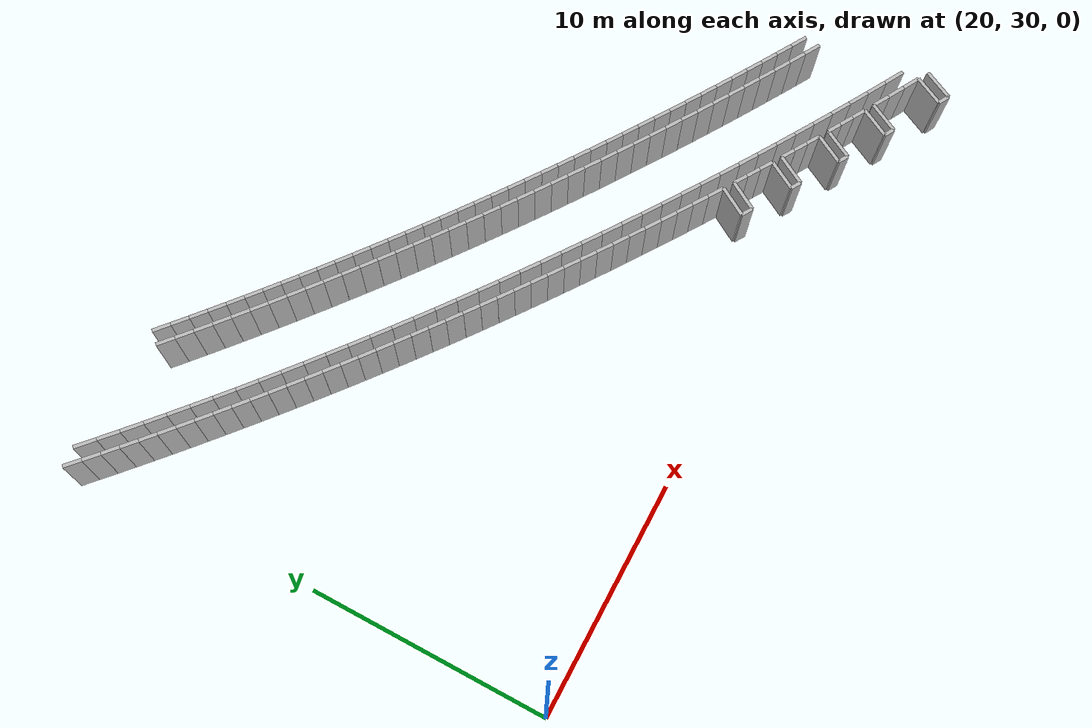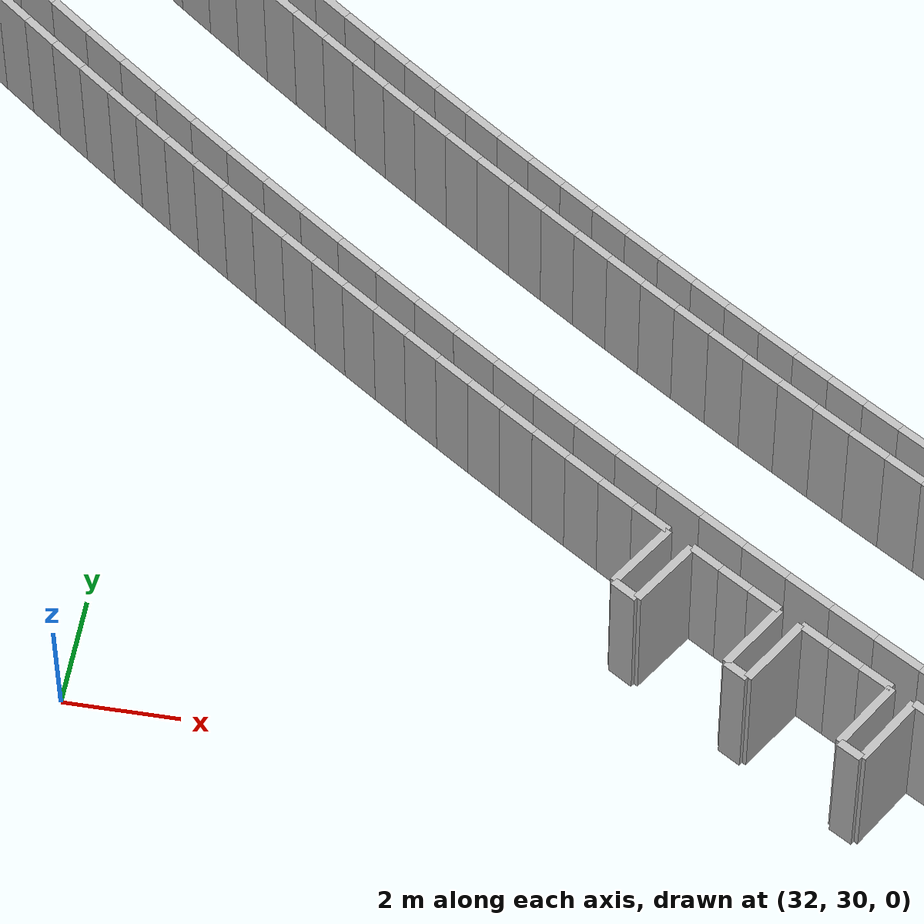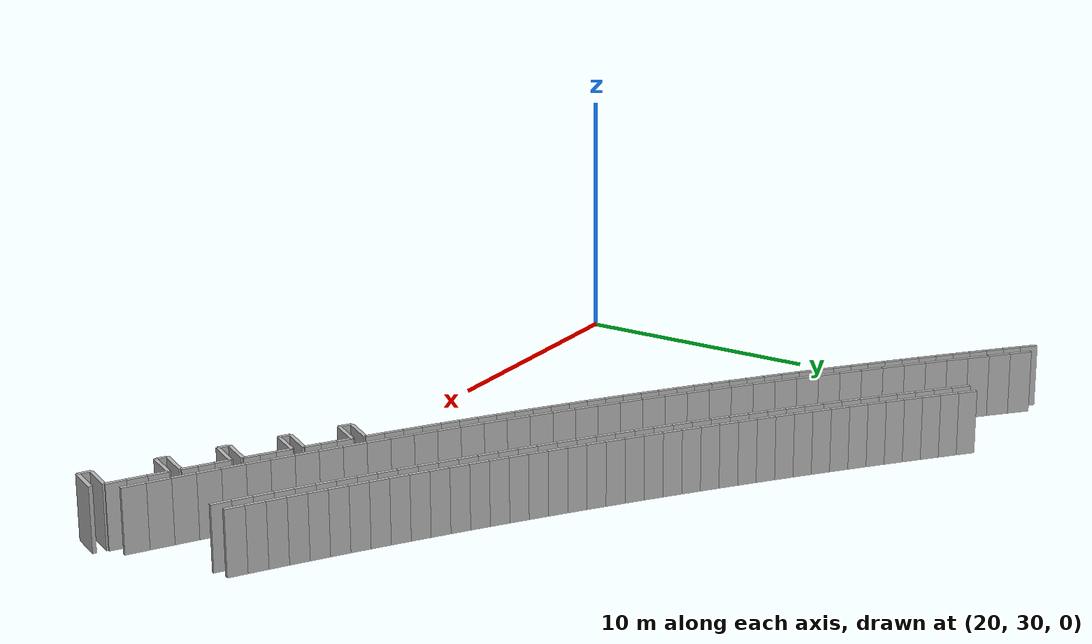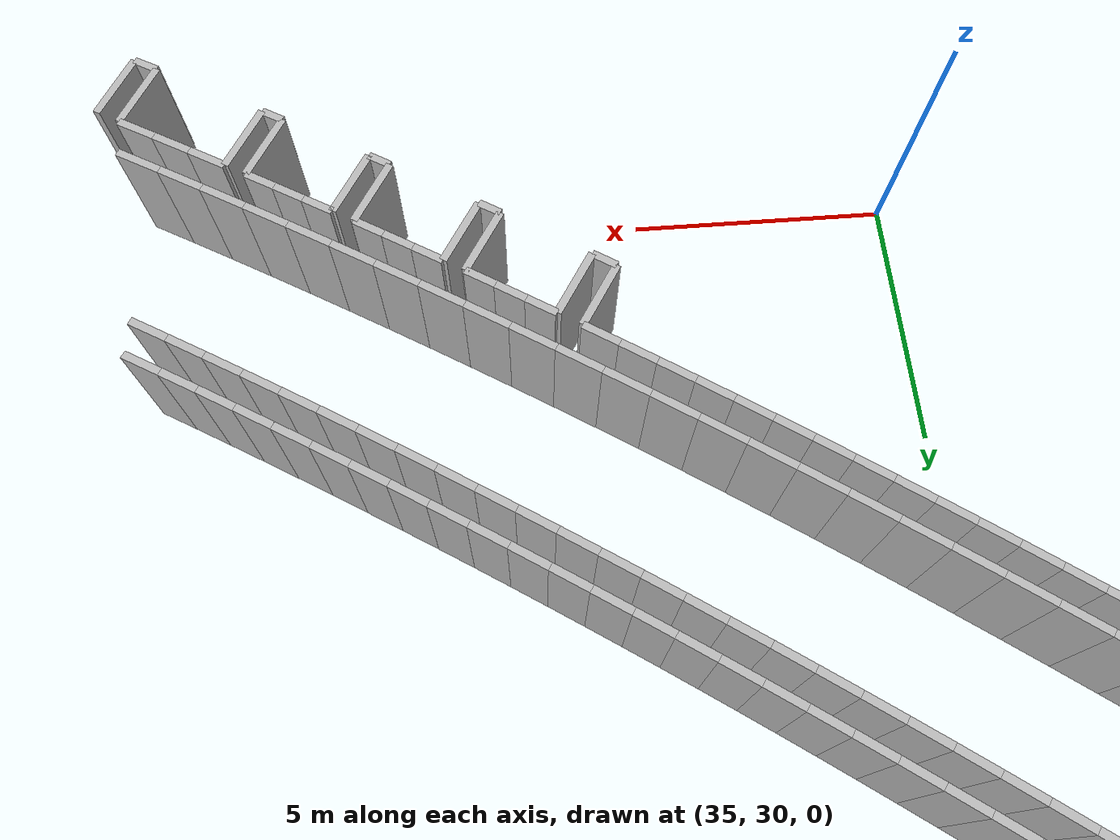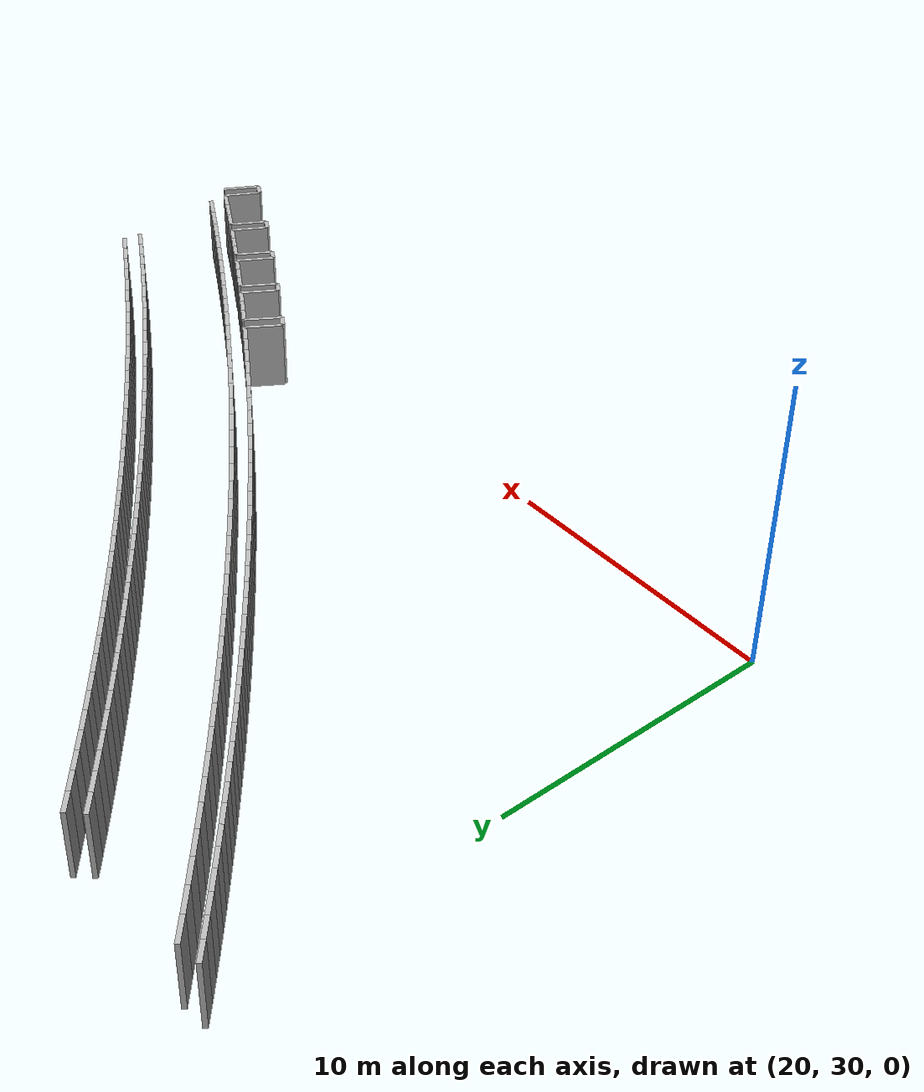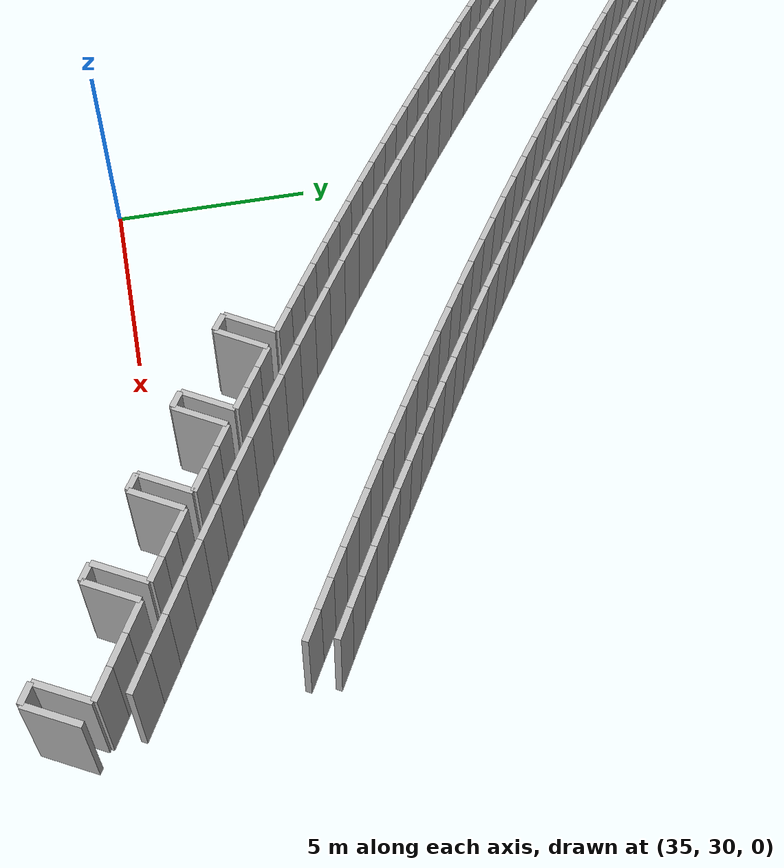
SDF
<?xml version="1.0" ?>
<sdf version="1.6">
  <model name="sps_0200">
    <pose frame="">0 0 0 0 -0 0</pose>
    <static>1</static>
    <self_collide>0</self_collide>
    <allow_auto_disable>0</allow_auto_disable>
    <link name="Wall40">
      <kinematic>0</kinematic>
      <gravity>1</gravity>
      <self_collide>0</self_collide>
      <collision name="collision">
        <geometry>
          <box>
            <size>0.49969 0.15 2.5</size>
          </box>
        </geometry>
        <pose frame="">0 0 0 0 -0 0</pose>
      </collision>
      <visual name="visual">
        <geometry>
          <box>
            <size>0.49969 0.15 2.5</size>
          </box>
        </geometry>
        <pose frame="">0 0 0 0 -0 0</pose>
        <cast_shadows>1</cast_shadows>
        <transparency>0.0</transparency>
      </visual>
      <pose frame="">40.9885 32.0877 1.25 0 -0 2.58012</pose>
    </link>
    <link name="Wall41">
      <kinematic>0</kinematic>
      <gravity>1</gravity>
      <self_collide>0</self_collide>
      <collision name="collision">
        <geometry>
          <box>
            <size>1.35028 0.15 2.5</size>
          </box>
        </geometry>
        <pose frame="">0 0 0 0 -0 0</pose>
      </collision>
      <visual name="visual">
        <geometry>
          <box>
            <size>1.35028 0.15 2.5</size>
          </box>
        </geometry>
        <pose frame="">0 0 0 0 -0 0</pose>
        <cast_shadows>1</cast_shadows>
        <transparency>0.0</transparency>
      </visual>
      <pose frame="">49.5522 27.8344 1.25 0 -0 1.07025</pose>
    </link>
    <link name="Wall765">
      <kinematic>0</kinematic>
      <gravity>1</gravity>
      <self_collide>0</self_collide>
      <collision name="collision">
        <geometry>
          <box>
            <size>1.34983 0.15 2.5</size>
          </box>
        </geometry>
        <pose frame="">0 0 0 0 -0 0</pose>
      </collision>
      <visual name="visual">
        <geometry>
          <box>
            <size>1.34983 0.15 2.5</size>
          </box>
        </geometry>
        <pose frame="">0 0 0 0 -0 0</pose>
        <cast_shadows>1</cast_shadows>
        <transparency>0.0</transparency>
      </visual>
      <pose frame="">41.5593 32.526 1.25 0 0 -2.13221</pose>
    </link>
    <link name="Wall766">
      <kinematic>0</kinematic>
      <gravity>1</gravity>
      <self_collide>0</self_collide>
      <collision name="collision">
        <geometry>
          <box>
            <size>0.44993 0.15 2.5</size>
          </box>
        </geometry>
        <pose frame="">0 0 0 0 -0 0</pose>
      </collision>
      <visual name="visual">
        <geometry>
          <box>
            <size>0.44993 0.15 2.5</size>
          </box>
        </geometry>
        <pose frame="">0 0 0 0 -0 0</pose>
        <cast_shadows>1</cast_shadows>
        <transparency>0.0</transparency>
      </visual>
      <pose frame="">42.9849 30.8538 1.25 0 -0 2.5951</pose>
    </link>
    <link name="Wall767">
      <kinematic>0</kinematic>
      <gravity>1</gravity>
      <self_collide>0</self_collide>
      <collision name="collision">
        <geometry>
          <box>
            <size>0.449914 0.15 2.5</size>
          </box>
        </geometry>
        <pose frame="">0 0 0 0 -0 0</pose>
      </collision>
      <visual name="visual">
        <geometry>
          <box>
            <size>0.449914 0.15 2.5</size>
          </box>
        </geometry>
        <pose frame="">0 0 0 0 -0 0</pose>
        <cast_shadows>1</cast_shadows>
        <transparency>0.0</transparency>
      </visual>
      <pose frame="">46.9821 28.4996 1.25 0 -0 2.62405</pose>
    </link>
    <link name="Wall768">
      <kinematic>0</kinematic>
      <gravity>1</gravity>
      <self_collide>0</self_collide>
      <collision name="collision">
        <geometry>
          <box>
            <size>1.34973 0.15 2.5</size>
          </box>
        </geometry>
        <pose frame="">0 0 0 0 -0 0</pose>
      </collision>
      <visual name="visual">
        <geometry>
          <box>
            <size>1.34973 0.15 2.5</size>
          </box>
        </geometry>
        <pose frame="">0 0 0 0 -0 0</pose>
        <cast_shadows>1</cast_shadows>
        <transparency>0.0</transparency>
      </visual>
      <pose frame="">47.1211 29.1971 1.25 0 -0 1.05236</pose>
    </link>
    <link name="Wall769">
      <kinematic>0</kinematic>
      <gravity>1</gravity>
      <self_collide>0</self_collide>
      <collision name="collision">
        <geometry>
          <box>
            <size>1.34973 0.15 2.5</size>
          </box>
        </geometry>
        <pose frame="">0 0 0 0 -0 0</pose>
      </collision>
      <visual name="visual">
        <geometry>
          <box>
            <size>1.34973 0.15 2.5</size>
          </box>
        </geometry>
        <pose frame="">0 0 0 0 -0 0</pose>
        <cast_shadows>1</cast_shadows>
        <transparency>0.0</transparency>
      </visual>
      <pose frame="">47.512 28.9745 1.25 0 0 -2.08924</pose>
    </link>
    <link name="Wall770">
      <kinematic>0</kinematic>
      <gravity>1</gravity>
      <self_collide>0</self_collide>
      <collision name="collision">
        <geometry>
          <box>
            <size>0.499964 0.15 2.5</size>
          </box>
        </geometry>
        <pose frame="">0 0 0 0 -0 0</pose>
      </collision>
      <visual name="visual">
        <geometry>
          <box>
            <size>0.499964 0.15 2.5</size>
          </box>
        </geometry>
        <pose frame="">0 0 0 0 -0 0</pose>
        <cast_shadows>1</cast_shadows>
        <transparency>0.0</transparency>
      </visual>
      <pose frame="">49.4475 27.1221 1.25 0 -0 2.64092</pose>
    </link>
    <link name="Wall1489">
      <kinematic>0</kinematic>
      <gravity>1</gravity>
      <self_collide>0</self_collide>
      <collision name="collision">
        <geometry>
          <box>
            <size>1.34995 0.15 2.5</size>
          </box>
        </geometry>
        <pose frame="">0 0 0 0 -0 0</pose>
      </collision>
      <visual name="visual">
        <geometry>
          <box>
            <size>1.34995 0.15 2.5</size>
          </box>
        </geometry>
        <pose frame="">0 0 0 0 -0 0</pose>
        <cast_shadows>1</cast_shadows>
        <transparency>0.0</transparency>
      </visual>
      <pose frame="">43.528 31.3135 1.25 0 0 -2.11748</pose>
    </link>
    <link name="Wall1490">
      <kinematic>0</kinematic>
      <gravity>1</gravity>
      <self_collide>0</self_collide>
      <collision name="collision">
        <geometry>
          <box>
            <size>1.35023 0.15 2.5</size>
          </box>
        </geometry>
        <pose frame="">0 0 0 0 -0 0</pose>
      </collision>
      <visual name="visual">
        <geometry>
          <box>
            <size>1.35023 0.15 2.5</size>
          </box>
        </geometry>
        <pose frame="">0 0 0 0 -0 0</pose>
        <cast_shadows>1</cast_shadows>
        <transparency>0.0</transparency>
      </visual>
      <pose frame="">45.1243 30.3581 1.25 0 -0 1.0382</pose>
    </link>
    <link name="Wall1786">
      <kinematic>0</kinematic>
      <gravity>1</gravity>
      <self_collide>0</self_collide>
      <collision name="collision">
        <geometry>
          <box>
            <size>1.34995 0.15 2.5</size>
          </box>
        </geometry>
        <pose frame="">0 0 0 0 -0 0</pose>
      </collision>
      <visual name="visual">
        <geometry>
          <box>
            <size>1.34995 0.15 2.5</size>
          </box>
        </geometry>
        <pose frame="">0 0 0 0 -0 0</pose>
        <cast_shadows>1</cast_shadows>
        <transparency>0.0</transparency>
      </visual>
      <pose frame="">43.1436 31.5473 1.25 0 -0 1.02411</pose>
    </link>
    <link name="Wall1787">
      <kinematic>0</kinematic>
      <gravity>1</gravity>
      <self_collide>0</self_collide>
      <collision name="collision">
        <geometry>
          <box>
            <size>0.450383 0.15 2.5</size>
          </box>
        </geometry>
        <pose frame="">0 0 0 0 -0 0</pose>
      </collision>
      <visual name="visual">
        <geometry>
          <box>
            <size>0.450383 0.15 2.5</size>
          </box>
        </geometry>
        <pose frame="">0 0 0 0 -0 0</pose>
        <cast_shadows>1</cast_shadows>
        <transparency>0.0</transparency>
      </visual>
      <pose frame="">44.9754 29.662 1.25 0 -0 2.60819</pose>
    </link>
    <link name="Wall2129">
      <kinematic>0</kinematic>
      <gravity>1</gravity>
      <self_collide>0</self_collide>
      <collision name="collision">
        <geometry>
          <box>
            <size>1.35023 0.15 2.5</size>
          </box>
        </geometry>
        <pose frame="">0 0 0 0 -0 0</pose>
      </collision>
      <visual name="visual">
        <geometry>
          <box>
            <size>1.35023 0.15 2.5</size>
          </box>
        </geometry>
        <pose frame="">0 0 0 0 -0 0</pose>
        <cast_shadows>1</cast_shadows>
        <transparency>0.0</transparency>
      </visual>
      <pose frame="">45.5121 30.1291 1.25 0 0 -2.10339</pose>
    </link>
    <link name="Wall2131">
      <kinematic>0</kinematic>
      <gravity>1</gravity>
      <self_collide>0</self_collide>
      <collision name="collision">
        <geometry>
          <box>
            <size>1.35007 0.15 2.5</size>
          </box>
        </geometry>
        <pose frame="">0 0 0 0 -0 0</pose>
      </collision>
      <visual name="visual">
        <geometry>
          <box>
            <size>1.35007 0.15 2.5</size>
          </box>
        </geometry>
        <pose frame="">0 0 0 0 -0 0</pose>
        <cast_shadows>1</cast_shadows>
        <transparency>0.0</transparency>
      </visual>
      <pose frame="">49.9908 27.5943 1.25 0 0 -2.07143</pose>
    </link>
    <link name="Wall2511">
      <kinematic>0</kinematic>
      <gravity>1</gravity>
      <self_collide>0</self_collide>
      <collision name="collision">
        <geometry>
          <box>
            <size>1.34969 0.15 2.5</size>
          </box>
        </geometry>
        <pose frame="">0 0 0 0 -0 0</pose>
      </collision>
      <visual name="visual">
        <geometry>
          <box>
            <size>1.34969 0.15 2.5</size>
          </box>
        </geometry>
        <pose frame="">0 0 0 0 -0 0</pose>
        <cast_shadows>1</cast_shadows>
        <transparency>0.0</transparency>
      </visual>
      <pose frame="">41.1359 32.7922 1.25 0 -0 1.01006</pose>
    </link>
    <link name="Wall6516">
      <kinematic>0</kinematic>
      <gravity>1</gravity>
      <self_collide>0</self_collide>
      <collision name="collision">
        <geometry>
          <box>
            <size>0.733459 0.15 2.5</size>
          </box>
        </geometry>
        <pose frame="">0 0 0 0 -0 0</pose>
      </collision>
      <visual name="visual">
        <geometry>
          <box>
            <size>0.733459 0.15 2.5</size>
          </box>
        </geometry>
        <pose frame="">0 0 0 0 -0 0</pose>
        <cast_shadows>1</cast_shadows>
        <transparency>0.0</transparency>
      </visual>
      <pose frame="">19.5955 49.929 1.25 0 0 -0.73271</pose>
    </link>
    <link name="Wall6517">
      <kinematic>0</kinematic>
      <gravity>1</gravity>
      <self_collide>0</self_collide>
      <collision name="collision">
        <geometry>
          <box>
            <size>0.73304 0.15 2.5</size>
          </box>
        </geometry>
        <pose frame="">0 0 0 0 -0 0</pose>
      </collision>
      <visual name="visual">
        <geometry>
          <box>
            <size>0.73304 0.15 2.5</size>
          </box>
        </geometry>
        <pose frame="">0 0 0 0 -0 0</pose>
        <cast_shadows>1</cast_shadows>
        <transparency>0.0</transparency>
      </visual>
      <pose frame="">20.1417 49.4398 1.25 0 0 -0.728081</pose>
    </link>
    <link name="Wall6518">
      <kinematic>0</kinematic>
      <gravity>1</gravity>
      <self_collide>0</self_collide>
      <collision name="collision">
        <geometry>
          <box>
            <size>0.732966 0.15 2.5</size>
          </box>
        </geometry>
        <pose frame="">0 0 0 0 -0 0</pose>
      </collision>
      <visual name="visual">
        <geometry>
          <box>
            <size>0.732966 0.15 2.5</size>
          </box>
        </geometry>
        <pose frame="">0 0 0 0 -0 0</pose>
        <cast_shadows>1</cast_shadows>
        <transparency>0.0</transparency>
      </visual>
      <pose frame="">20.6898 48.9532 1.25 0 0 -0.723828</pose>
    </link>
    <link name="Wall6519">
      <kinematic>0</kinematic>
      <gravity>1</gravity>
      <self_collide>0</self_collide>
      <collision name="collision">
        <geometry>
          <box>
            <size>0.733066 0.15 2.5</size>
          </box>
        </geometry>
        <pose frame="">0 0 0 0 -0 0</pose>
      </collision>
      <visual name="visual">
        <geometry>
          <box>
            <size>0.733066 0.15 2.5</size>
          </box>
        </geometry>
        <pose frame="">0 0 0 0 -0 0</pose>
        <cast_shadows>1</cast_shadows>
        <transparency>0.0</transparency>
      </visual>
      <pose frame="">21.2403 48.4691 1.25 0 0 -0.71894</pose>
    </link>
    <link name="Wall6520">
      <kinematic>0</kinematic>
      <gravity>1</gravity>
      <self_collide>0</self_collide>
      <collision name="collision">
        <geometry>
          <box>
            <size>0.733113 0.15 2.5</size>
          </box>
        </geometry>
        <pose frame="">0 0 0 0 -0 0</pose>
      </collision>
      <visual name="visual">
        <geometry>
          <box>
            <size>0.733113 0.15 2.5</size>
          </box>
        </geometry>
        <pose frame="">0 0 0 0 -0 0</pose>
        <cast_shadows>1</cast_shadows>
        <transparency>0.0</transparency>
      </visual>
      <pose frame="">21.793 47.9875 1.25 0 0 -0.714577</pose>
    </link>
    <link name="Wall6521">
      <kinematic>0</kinematic>
      <gravity>1</gravity>
      <self_collide>0</self_collide>
      <collision name="collision">
        <geometry>
          <box>
            <size>0.733227 0.15 2.5</size>
          </box>
        </geometry>
        <pose frame="">0 0 0 0 -0 0</pose>
      </collision>
      <visual name="visual">
        <geometry>
          <box>
            <size>0.733227 0.15 2.5</size>
          </box>
        </geometry>
        <pose frame="">0 0 0 0 -0 0</pose>
        <cast_shadows>1</cast_shadows>
        <transparency>0.0</transparency>
      </visual>
      <pose frame="">22.3479 47.5083 1.25 0 0 -0.710044</pose>
    </link>
    <link name="Wall6522">
      <kinematic>0</kinematic>
      <gravity>1</gravity>
      <self_collide>0</self_collide>
      <collision name="collision">
        <geometry>
          <box>
            <size>0.733065 0.15 2.5</size>
          </box>
        </geometry>
        <pose frame="">0 0 0 0 -0 0</pose>
      </collision>
      <visual name="visual">
        <geometry>
          <box>
            <size>0.733065 0.15 2.5</size>
          </box>
        </geometry>
        <pose frame="">0 0 0 0 -0 0</pose>
        <cast_shadows>1</cast_shadows>
        <transparency>0.0</transparency>
      </visual>
      <pose frame="">22.905 47.0317 1.25 0 0 -0.705303</pose>
    </link>
    <link name="Wall6523">
      <kinematic>0</kinematic>
      <gravity>1</gravity>
      <self_collide>0</self_collide>
      <collision name="collision">
        <geometry>
          <box>
            <size>0.733069 0.15 2.5</size>
          </box>
        </geometry>
        <pose frame="">0 0 0 0 -0 0</pose>
      </collision>
      <visual name="visual">
        <geometry>
          <box>
            <size>0.733069 0.15 2.5</size>
          </box>
        </geometry>
        <pose frame="">0 0 0 0 -0 0</pose>
        <cast_shadows>1</cast_shadows>
        <transparency>0.0</transparency>
      </visual>
      <pose frame="">23.4642 46.5577 1.25 0 0 -0.700932</pose>
    </link>
    <link name="Wall6524">
      <kinematic>0</kinematic>
      <gravity>1</gravity>
      <self_collide>0</self_collide>
      <collision name="collision">
        <geometry>
          <box>
            <size>0.733314 0.15 2.5</size>
          </box>
        </geometry>
        <pose frame="">0 0 0 0 -0 0</pose>
      </collision>
      <visual name="visual">
        <geometry>
          <box>
            <size>0.733314 0.15 2.5</size>
          </box>
        </geometry>
        <pose frame="">0 0 0 0 -0 0</pose>
        <cast_shadows>1</cast_shadows>
        <transparency>0.0</transparency>
      </visual>
      <pose frame="">24.0256 46.0861 1.25 0 0 -0.696411</pose>
    </link>
    <link name="Wall6525">
      <kinematic>0</kinematic>
      <gravity>1</gravity>
      <self_collide>0</self_collide>
      <collision name="collision">
        <geometry>
          <box>
            <size>0.733081 0.15 2.5</size>
          </box>
        </geometry>
        <pose frame="">0 0 0 0 -0 0</pose>
      </collision>
      <visual name="visual">
        <geometry>
          <box>
            <size>0.733081 0.15 2.5</size>
          </box>
        </geometry>
        <pose frame="">0 0 0 0 -0 0</pose>
        <cast_shadows>1</cast_shadows>
        <transparency>0.0</transparency>
      </visual>
      <pose frame="">24.589 45.617 1.25 0 0 -0.692127</pose>
    </link>
    <link name="Wall6526">
      <kinematic>0</kinematic>
      <gravity>1</gravity>
      <self_collide>0</self_collide>
      <collision name="collision">
        <geometry>
          <box>
            <size>0.732951 0.15 2.5</size>
          </box>
        </geometry>
        <pose frame="">0 0 0 0 -0 0</pose>
      </collision>
      <visual name="visual">
        <geometry>
          <box>
            <size>0.732951 0.15 2.5</size>
          </box>
        </geometry>
        <pose frame="">0 0 0 0 -0 0</pose>
        <cast_shadows>1</cast_shadows>
        <transparency>0.0</transparency>
      </visual>
      <pose frame="">25.1545 45.1506 1.25 0 0 -0.6872</pose>
    </link>
    <link name="Wall6527">
      <kinematic>0</kinematic>
      <gravity>1</gravity>
      <self_collide>0</self_collide>
      <collision name="collision">
        <geometry>
          <box>
            <size>0.733194 0.15 2.5</size>
          </box>
        </geometry>
        <pose frame="">0 0 0 0 -0 0</pose>
      </collision>
      <visual name="visual">
        <geometry>
          <box>
            <size>0.733194 0.15 2.5</size>
          </box>
        </geometry>
        <pose frame="">0 0 0 0 -0 0</pose>
        <cast_shadows>1</cast_shadows>
        <transparency>0.0</transparency>
      </visual>
      <pose frame="">25.7223 44.6868 1.25 0 0 -0.682737</pose>
    </link>
    <link name="Wall6528">
      <kinematic>0</kinematic>
      <gravity>1</gravity>
      <self_collide>0</self_collide>
      <collision name="collision">
        <geometry>
          <box>
            <size>0.733241 0.15 2.5</size>
          </box>
        </geometry>
        <pose frame="">0 0 0 0 -0 0</pose>
      </collision>
      <visual name="visual">
        <geometry>
          <box>
            <size>0.733241 0.15 2.5</size>
          </box>
        </geometry>
        <pose frame="">0 0 0 0 -0 0</pose>
        <cast_shadows>1</cast_shadows>
        <transparency>0.0</transparency>
      </visual>
      <pose frame="">26.2922 44.2255 1.25 0 0 -0.678186</pose>
    </link>
    <link name="Wall6529">
      <kinematic>0</kinematic>
      <gravity>1</gravity>
      <self_collide>0</self_collide>
      <collision name="collision">
        <geometry>
          <box>
            <size>0.733171 0.15 2.5</size>
          </box>
        </geometry>
        <pose frame="">0 0 0 0 -0 0</pose>
      </collision>
      <visual name="visual">
        <geometry>
          <box>
            <size>0.733171 0.15 2.5</size>
          </box>
        </geometry>
        <pose frame="">0 0 0 0 -0 0</pose>
        <cast_shadows>1</cast_shadows>
        <transparency>0.0</transparency>
      </visual>
      <pose frame="">26.8642 43.7668 1.25 0 0 -0.673675</pose>
    </link>
    <link name="Wall6530">
      <kinematic>0</kinematic>
      <gravity>1</gravity>
      <self_collide>0</self_collide>
      <collision name="collision">
        <geometry>
          <box>
            <size>0.733153 0.15 2.5</size>
          </box>
        </geometry>
        <pose frame="">0 0 0 0 -0 0</pose>
      </collision>
      <visual name="visual">
        <geometry>
          <box>
            <size>0.733153 0.15 2.5</size>
          </box>
        </geometry>
        <pose frame="">0 0 0 0 -0 0</pose>
        <cast_shadows>1</cast_shadows>
        <transparency>0.0</transparency>
      </visual>
      <pose frame="">27.4382 43.3107 1.25 0 0 -0.669228</pose>
    </link>
    <link name="Wall6531">
      <kinematic>0</kinematic>
      <gravity>1</gravity>
      <self_collide>0</self_collide>
      <collision name="collision">
        <geometry>
          <box>
            <size>0.732913 0.15 2.5</size>
          </box>
        </geometry>
        <pose frame="">0 0 0 0 -0 0</pose>
      </collision>
      <visual name="visual">
        <geometry>
          <box>
            <size>0.732913 0.15 2.5</size>
          </box>
        </geometry>
        <pose frame="">0 0 0 0 -0 0</pose>
        <cast_shadows>1</cast_shadows>
        <transparency>0.0</transparency>
      </visual>
      <pose frame="">28.0142 42.8573 1.25 0 0 -0.664505</pose>
    </link>
    <link name="Wall6532">
      <kinematic>0</kinematic>
      <gravity>1</gravity>
      <self_collide>0</self_collide>
      <collision name="collision">
        <geometry>
          <box>
            <size>0.73323 0.15 2.5</size>
          </box>
        </geometry>
        <pose frame="">0 0 0 0 -0 0</pose>
      </collision>
      <visual name="visual">
        <geometry>
          <box>
            <size>0.73323 0.15 2.5</size>
          </box>
        </geometry>
        <pose frame="">0 0 0 0 -0 0</pose>
        <cast_shadows>1</cast_shadows>
        <transparency>0.0</transparency>
      </visual>
      <pose frame="">28.5922 42.4065 1.25 0 0 -0.66005</pose>
    </link>
    <link name="Wall6533">
      <kinematic>0</kinematic>
      <gravity>1</gravity>
      <self_collide>0</self_collide>
      <collision name="collision">
        <geometry>
          <box>
            <size>0.733097 0.15 2.5</size>
          </box>
        </geometry>
        <pose frame="">0 0 0 0 -0 0</pose>
      </collision>
      <visual name="visual">
        <geometry>
          <box>
            <size>0.733097 0.15 2.5</size>
          </box>
        </geometry>
        <pose frame="">0 0 0 0 -0 0</pose>
        <cast_shadows>1</cast_shadows>
        <transparency>0.0</transparency>
      </visual>
      <pose frame="">29.1724 41.9583 1.25 0 0 -0.655457</pose>
    </link>
    <link name="Wall6534">
      <kinematic>0</kinematic>
      <gravity>1</gravity>
      <self_collide>0</self_collide>
      <collision name="collision">
        <geometry>
          <box>
            <size>0.732956 0.15 2.5</size>
          </box>
        </geometry>
        <pose frame="">0 0 0 0 -0 0</pose>
      </collision>
      <visual name="visual">
        <geometry>
          <box>
            <size>0.732956 0.15 2.5</size>
          </box>
        </geometry>
        <pose frame="">0 0 0 0 -0 0</pose>
        <cast_shadows>1</cast_shadows>
        <transparency>0.0</transparency>
      </visual>
      <pose frame="">29.7545 41.5128 1.25 0 0 -0.651096</pose>
    </link>
    <link name="Wall6535">
      <kinematic>0</kinematic>
      <gravity>1</gravity>
      <self_collide>0</self_collide>
      <collision name="collision">
        <geometry>
          <box>
            <size>0.733121 0.15 2.5</size>
          </box>
        </geometry>
        <pose frame="">0 0 0 0 -0 0</pose>
      </collision>
      <visual name="visual">
        <geometry>
          <box>
            <size>0.733121 0.15 2.5</size>
          </box>
        </geometry>
        <pose frame="">0 0 0 0 -0 0</pose>
        <cast_shadows>1</cast_shadows>
        <transparency>0.0</transparency>
      </visual>
      <pose frame="">30.3386 41.0699 1.25 0 0 -0.646432</pose>
    </link>
    <link name="Wall6536">
      <kinematic>0</kinematic>
      <gravity>1</gravity>
      <self_collide>0</self_collide>
      <collision name="collision">
        <geometry>
          <box>
            <size>0.733155 0.15 2.5</size>
          </box>
        </geometry>
        <pose frame="">0 0 0 0 -0 0</pose>
      </collision>
      <visual name="visual">
        <geometry>
          <box>
            <size>0.733155 0.15 2.5</size>
          </box>
        </geometry>
        <pose frame="">0 0 0 0 -0 0</pose>
        <cast_shadows>1</cast_shadows>
        <transparency>0.0</transparency>
      </visual>
      <pose frame="">30.9249 40.6296 1.25 0 0 -0.641919</pose>
    </link>
    <link name="Wall6537">
      <kinematic>0</kinematic>
      <gravity>1</gravity>
      <self_collide>0</self_collide>
      <collision name="collision">
        <geometry>
          <box>
            <size>0.733083 0.15 2.5</size>
          </box>
        </geometry>
        <pose frame="">0 0 0 0 -0 0</pose>
      </collision>
      <visual name="visual">
        <geometry>
          <box>
            <size>0.733083 0.15 2.5</size>
          </box>
        </geometry>
        <pose frame="">0 0 0 0 -0 0</pose>
        <cast_shadows>1</cast_shadows>
        <transparency>0.0</transparency>
      </visual>
      <pose frame="">31.5131 40.192 1.25 0 0 -0.637323</pose>
    </link>
    <link name="Wall6538">
      <kinematic>0</kinematic>
      <gravity>1</gravity>
      <self_collide>0</self_collide>
      <collision name="collision">
        <geometry>
          <box>
            <size>0.733147 0.15 2.5</size>
          </box>
        </geometry>
        <pose frame="">0 0 0 0 -0 0</pose>
      </collision>
      <visual name="visual">
        <geometry>
          <box>
            <size>0.733147 0.15 2.5</size>
          </box>
        </geometry>
        <pose frame="">0 0 0 0 -0 0</pose>
        <cast_shadows>1</cast_shadows>
        <transparency>0.0</transparency>
      </visual>
      <pose frame="">32.1032 39.7571 1.25 0 0 -0.632811</pose>
    </link>
    <link name="Wall6539">
      <kinematic>0</kinematic>
      <gravity>1</gravity>
      <self_collide>0</self_collide>
      <collision name="collision">
        <geometry>
          <box>
            <size>0.732971 0.15 2.5</size>
          </box>
        </geometry>
        <pose frame="">0 0 0 0 -0 0</pose>
      </collision>
      <visual name="visual">
        <geometry>
          <box>
            <size>0.732971 0.15 2.5</size>
          </box>
        </geometry>
        <pose frame="">0 0 0 0 -0 0</pose>
        <cast_shadows>1</cast_shadows>
        <transparency>0.0</transparency>
      </visual>
      <pose frame="">32.6953 39.3249 1.25 0 0 -0.628245</pose>
    </link>
    <link name="Wall6540">
      <kinematic>0</kinematic>
      <gravity>1</gravity>
      <self_collide>0</self_collide>
      <collision name="collision">
        <geometry>
          <box>
            <size>0.73325 0.15 2.5</size>
          </box>
        </geometry>
        <pose frame="">0 0 0 0 -0 0</pose>
      </collision>
      <visual name="visual">
        <geometry>
          <box>
            <size>0.73325 0.15 2.5</size>
          </box>
        </geometry>
        <pose frame="">0 0 0 0 -0 0</pose>
        <cast_shadows>1</cast_shadows>
        <transparency>0.0</transparency>
      </visual>
      <pose frame="">33.2895 38.8954 1.25 0 0 -0.623656</pose>
    </link>
    <link name="Wall6541">
      <kinematic>0</kinematic>
      <gravity>1</gravity>
      <self_collide>0</self_collide>
      <collision name="collision">
        <geometry>
          <box>
            <size>0.733161 0.15 2.5</size>
          </box>
        </geometry>
        <pose frame="">0 0 0 0 -0 0</pose>
      </collision>
      <visual name="visual">
        <geometry>
          <box>
            <size>0.733161 0.15 2.5</size>
          </box>
        </geometry>
        <pose frame="">0 0 0 0 -0 0</pose>
        <cast_shadows>1</cast_shadows>
        <transparency>0.0</transparency>
      </visual>
      <pose frame="">33.8856 38.4685 1.25 0 0 -0.61934</pose>
    </link>
    <link name="Wall6542">
      <kinematic>0</kinematic>
      <gravity>1</gravity>
      <self_collide>0</self_collide>
      <collision name="collision">
        <geometry>
          <box>
            <size>0.733179 0.15 2.5</size>
          </box>
        </geometry>
        <pose frame="">0 0 0 0 -0 0</pose>
      </collision>
      <visual name="visual">
        <geometry>
          <box>
            <size>0.733179 0.15 2.5</size>
          </box>
        </geometry>
        <pose frame="">0 0 0 0 -0 0</pose>
        <cast_shadows>1</cast_shadows>
        <transparency>0.0</transparency>
      </visual>
      <pose frame="">34.4835 38.0443 1.25 0 0 -0.614627</pose>
    </link>
    <link name="Wall6543">
      <kinematic>0</kinematic>
      <gravity>1</gravity>
      <self_collide>0</self_collide>
      <collision name="collision">
        <geometry>
          <box>
            <size>0.733204 0.15 2.5</size>
          </box>
        </geometry>
        <pose frame="">0 0 0 0 -0 0</pose>
      </collision>
      <visual name="visual">
        <geometry>
          <box>
            <size>0.733204 0.15 2.5</size>
          </box>
        </geometry>
        <pose frame="">0 0 0 0 -0 0</pose>
        <cast_shadows>1</cast_shadows>
        <transparency>0.0</transparency>
      </visual>
      <pose frame="">35.0835 37.6228 1.25 0 0 -0.61033</pose>
    </link>
    <link name="Wall6544">
      <kinematic>0</kinematic>
      <gravity>1</gravity>
      <self_collide>0</self_collide>
      <collision name="collision">
        <geometry>
          <box>
            <size>0.733064 0.15 2.5</size>
          </box>
        </geometry>
        <pose frame="">0 0 0 0 -0 0</pose>
      </collision>
      <visual name="visual">
        <geometry>
          <box>
            <size>0.733064 0.15 2.5</size>
          </box>
        </geometry>
        <pose frame="">0 0 0 0 -0 0</pose>
        <cast_shadows>1</cast_shadows>
        <transparency>0.0</transparency>
      </visual>
      <pose frame="">35.6853 37.2041 1.25 0 0 -0.605392</pose>
    </link>
    <link name="Wall6545">
      <kinematic>0</kinematic>
      <gravity>1</gravity>
      <self_collide>0</self_collide>
      <collision name="collision">
        <geometry>
          <box>
            <size>0.733118 0.15 2.5</size>
          </box>
        </geometry>
        <pose frame="">0 0 0 0 -0 0</pose>
      </collision>
      <visual name="visual">
        <geometry>
          <box>
            <size>0.733118 0.15 2.5</size>
          </box>
        </geometry>
        <pose frame="">0 0 0 0 -0 0</pose>
        <cast_shadows>1</cast_shadows>
        <transparency>0.0</transparency>
      </visual>
      <pose frame="">36.289 36.7882 1.25 0 0 -0.601095</pose>
    </link>
    <link name="Wall6546">
      <kinematic>0</kinematic>
      <gravity>1</gravity>
      <self_collide>0</self_collide>
      <collision name="collision">
        <geometry>
          <box>
            <size>0.732997 0.15 2.5</size>
          </box>
        </geometry>
        <pose frame="">0 0 0 0 -0 0</pose>
      </collision>
      <visual name="visual">
        <geometry>
          <box>
            <size>0.732997 0.15 2.5</size>
          </box>
        </geometry>
        <pose frame="">0 0 0 0 -0 0</pose>
        <cast_shadows>1</cast_shadows>
        <transparency>0.0</transparency>
      </visual>
      <pose frame="">36.8945 36.375 1.25 0 0 -0.596571</pose>
    </link>
    <link name="Wall6547">
      <kinematic>0</kinematic>
      <gravity>1</gravity>
      <self_collide>0</self_collide>
      <collision name="collision">
        <geometry>
          <box>
            <size>0.733196 0.15 2.5</size>
          </box>
        </geometry>
        <pose frame="">0 0 0 0 -0 0</pose>
      </collision>
      <visual name="visual">
        <geometry>
          <box>
            <size>0.733196 0.15 2.5</size>
          </box>
        </geometry>
        <pose frame="">0 0 0 0 -0 0</pose>
        <cast_shadows>1</cast_shadows>
        <transparency>0.0</transparency>
      </visual>
      <pose frame="">37.5019 35.9645 1.25 0 0 -0.592066</pose>
    </link>
    <link name="Wall6548">
      <kinematic>0</kinematic>
      <gravity>1</gravity>
      <self_collide>0</self_collide>
      <collision name="collision">
        <geometry>
          <box>
            <size>0.73319 0.15 2.5</size>
          </box>
        </geometry>
        <pose frame="">0 0 0 0 -0 0</pose>
      </collision>
      <visual name="visual">
        <geometry>
          <box>
            <size>0.73319 0.15 2.5</size>
          </box>
        </geometry>
        <pose frame="">0 0 0 0 -0 0</pose>
        <cast_shadows>1</cast_shadows>
        <transparency>0.0</transparency>
      </visual>
      <pose frame="">38.1112 35.5567 1.25 0 0 -0.587564</pose>
    </link>
    <link name="Wall6549">
      <kinematic>0</kinematic>
      <gravity>1</gravity>
      <self_collide>0</self_collide>
      <collision name="collision">
        <geometry>
          <box>
            <size>0.733081 0.15 2.5</size>
          </box>
        </geometry>
        <pose frame="">0 0 0 0 -0 0</pose>
      </collision>
      <visual name="visual">
        <geometry>
          <box>
            <size>0.733081 0.15 2.5</size>
          </box>
        </geometry>
        <pose frame="">0 0 0 0 -0 0</pose>
        <cast_shadows>1</cast_shadows>
        <transparency>0.0</transparency>
      </visual>
      <pose frame="">38.7223 35.1517 1.25 0 0 -0.582969</pose>
    </link>
    <link name="Wall6550">
      <kinematic>0</kinematic>
      <gravity>1</gravity>
      <self_collide>0</self_collide>
      <collision name="collision">
        <geometry>
          <box>
            <size>0.733207 0.15 2.5</size>
          </box>
        </geometry>
        <pose frame="">0 0 0 0 -0 0</pose>
      </collision>
      <visual name="visual">
        <geometry>
          <box>
            <size>0.733207 0.15 2.5</size>
          </box>
        </geometry>
        <pose frame="">0 0 0 0 -0 0</pose>
        <cast_shadows>1</cast_shadows>
        <transparency>0.0</transparency>
      </visual>
      <pose frame="">39.3353 34.7495 1.25 0 0 -0.578375</pose>
    </link>
    <link name="Wall6551">
      <kinematic>0</kinematic>
      <gravity>1</gravity>
      <self_collide>0</self_collide>
      <collision name="collision">
        <geometry>
          <box>
            <size>0.73306 0.15 2.5</size>
          </box>
        </geometry>
        <pose frame="">0 0 0 0 -0 0</pose>
      </collision>
      <visual name="visual">
        <geometry>
          <box>
            <size>0.73306 0.15 2.5</size>
          </box>
        </geometry>
        <pose frame="">0 0 0 0 -0 0</pose>
        <cast_shadows>1</cast_shadows>
        <transparency>0.0</transparency>
      </visual>
      <pose frame="">39.95 34.3501 1.25 0 0 -0.573939</pose>
    </link>
    <link name="Wall6552">
      <kinematic>0</kinematic>
      <gravity>1</gravity>
      <self_collide>0</self_collide>
      <collision name="collision">
        <geometry>
          <box>
            <size>0.733103 0.15 2.5</size>
          </box>
        </geometry>
        <pose frame="">0 0 0 0 -0 0</pose>
      </collision>
      <visual name="visual">
        <geometry>
          <box>
            <size>0.733103 0.15 2.5</size>
          </box>
        </geometry>
        <pose frame="">0 0 0 0 -0 0</pose>
        <cast_shadows>1</cast_shadows>
        <transparency>0.0</transparency>
      </visual>
      <pose frame="">40.5666 33.9536 1.25 0 0 -0.568951</pose>
    </link>
    <link name="Wall6553">
      <kinematic>0</kinematic>
      <gravity>1</gravity>
      <self_collide>0</self_collide>
      <collision name="collision">
        <geometry>
          <box>
            <size>0.73322 0.15 2.5</size>
          </box>
        </geometry>
        <pose frame="">0 0 0 0 -0 0</pose>
      </collision>
      <visual name="visual">
        <geometry>
          <box>
            <size>0.73322 0.15 2.5</size>
          </box>
        </geometry>
        <pose frame="">0 0 0 0 -0 0</pose>
        <cast_shadows>1</cast_shadows>
        <transparency>0.0</transparency>
      </visual>
      <pose frame="">41.1851 33.5599 1.25 0 0 -0.564705</pose>
    </link>
    <link name="Wall6554">
      <kinematic>0</kinematic>
      <gravity>1</gravity>
      <self_collide>0</self_collide>
      <collision name="collision">
        <geometry>
          <box>
            <size>0.775033 0.15 2.5</size>
          </box>
        </geometry>
        <pose frame="">0 0 0 0 -0 0</pose>
      </collision>
      <visual name="visual">
        <geometry>
          <box>
            <size>0.775033 0.15 2.5</size>
          </box>
        </geometry>
        <pose frame="">0 0 0 0 -0 0</pose>
        <cast_shadows>1</cast_shadows>
        <transparency>0.0</transparency>
      </visual>
      <pose frame="">49.537 28.6141 1.25 0 -0 2.6369</pose>
    </link>
    <link name="Wall6555">
      <kinematic>0</kinematic>
      <gravity>1</gravity>
      <self_collide>0</self_collide>
      <collision name="collision">
        <geometry>
          <box>
            <size>0.775033 0.15 2.5</size>
          </box>
        </geometry>
        <pose frame="">0 0 0 0 -0 0</pose>
      </collision>
      <visual name="visual">
        <geometry>
          <box>
            <size>0.775033 0.15 2.5</size>
          </box>
        </geometry>
        <pose frame="">0 0 0 0 -0 0</pose>
        <cast_shadows>1</cast_shadows>
        <transparency>0.0</transparency>
      </visual>
      <pose frame="">48.8595 28.9905 1.25 0 -0 2.63204</pose>
    </link>
    <link name="Wall6556">
      <kinematic>0</kinematic>
      <gravity>1</gravity>
      <self_collide>0</self_collide>
      <collision name="collision">
        <geometry>
          <box>
            <size>0.775015 0.15 2.5</size>
          </box>
        </geometry>
        <pose frame="">0 0 0 0 -0 0</pose>
      </collision>
      <visual name="visual">
        <geometry>
          <box>
            <size>0.775015 0.15 2.5</size>
          </box>
        </geometry>
        <pose frame="">0 0 0 0 -0 0</pose>
        <cast_shadows>1</cast_shadows>
        <transparency>0.0</transparency>
      </visual>
      <pose frame="">48.1839 29.3701 1.25 0 -0 2.62742</pose>
    </link>
    <link name="Wall16577">
      <kinematic>0</kinematic>
      <gravity>1</gravity>
      <self_collide>0</self_collide>
      <collision name="collision">
        <geometry>
          <box>
            <size>0.617301 0.15 2.5</size>
          </box>
        </geometry>
        <pose frame="">0 0 0 0 -0 0</pose>
      </collision>
      <visual name="visual">
        <geometry>
          <box>
            <size>0.617301 0.15 2.5</size>
          </box>
        </geometry>
        <pose frame="">0 0 0 0 -0 0</pose>
        <cast_shadows>1</cast_shadows>
        <transparency>0.0</transparency>
      </visual>
      <pose frame="">43.2313 32.2851 1.25 0 -0 2.5921</pose>
    </link>
    <link name="Wall16578">
      <kinematic>0</kinematic>
      <gravity>1</gravity>
      <self_collide>0</self_collide>
      <collision name="collision">
        <geometry>
          <box>
            <size>0.617472 0.15 2.5</size>
          </box>
        </geometry>
        <pose frame="">0 0 0 0 -0 0</pose>
      </collision>
      <visual name="visual">
        <geometry>
          <box>
            <size>0.617472 0.15 2.5</size>
          </box>
        </geometry>
        <pose frame="">0 0 0 0 -0 0</pose>
        <cast_shadows>1</cast_shadows>
        <transparency>0.0</transparency>
      </visual>
      <pose frame="">42.7053 32.6085 1.25 0 -0 2.58844</pose>
    </link>
    <link name="Wall16579">
      <kinematic>0</kinematic>
      <gravity>1</gravity>
      <self_collide>0</self_collide>
      <collision name="collision">
        <geometry>
          <box>
            <size>0.617438 0.15 2.5</size>
          </box>
        </geometry>
        <pose frame="">0 0 0 0 -0 0</pose>
      </collision>
      <visual name="visual">
        <geometry>
          <box>
            <size>0.617438 0.15 2.5</size>
          </box>
        </geometry>
        <pose frame="">0 0 0 0 -0 0</pose>
        <cast_shadows>1</cast_shadows>
        <transparency>0.0</transparency>
      </visual>
      <pose frame="">42.1807 32.934 1.25 0 -0 2.58422</pose>
    </link>
    <link name="Wall24536">
      <kinematic>0</kinematic>
      <gravity>1</gravity>
      <self_collide>0</self_collide>
      <collision name="collision">
        <geometry>
          <box>
            <size>0.913664 0.15 2.5</size>
          </box>
        </geometry>
        <pose frame="">0 0 0 0 -0 0</pose>
      </collision>
      <visual name="visual">
        <geometry>
          <box>
            <size>0.913664 0.15 2.5</size>
          </box>
        </geometry>
        <pose frame="">0 0 0 0 -0 0</pose>
        <cast_shadows>1</cast_shadows>
        <transparency>0.0</transparency>
      </visual>
      <pose frame="">20.4693 49.9519 1.25 0 0 -0.728684</pose>
    </link>
    <link name="Wall24537">
      <kinematic>0</kinematic>
      <gravity>1</gravity>
      <self_collide>0</self_collide>
      <collision name="collision">
        <geometry>
          <box>
            <size>0.9138 0.15 2.5</size>
          </box>
        </geometry>
        <pose frame="">0 0 0 0 -0 0</pose>
      </collision>
      <visual name="visual">
        <geometry>
          <box>
            <size>0.9138 0.15 2.5</size>
          </box>
        </geometry>
        <pose frame="">0 0 0 0 -0 0</pose>
        <cast_shadows>1</cast_shadows>
        <transparency>0.0</transparency>
      </visual>
      <pose frame="">21.1527 49.3454 1.25 0 0 -0.723015</pose>
    </link>
    <link name="Wall24538">
      <kinematic>0</kinematic>
      <gravity>1</gravity>
      <self_collide>0</self_collide>
      <collision name="collision">
        <geometry>
          <box>
            <size>0.913874 0.15 2.5</size>
          </box>
        </geometry>
        <pose frame="">0 0 0 0 -0 0</pose>
      </collision>
      <visual name="visual">
        <geometry>
          <box>
            <size>0.913874 0.15 2.5</size>
          </box>
        </geometry>
        <pose frame="">0 0 0 0 -0 0</pose>
        <cast_shadows>1</cast_shadows>
        <transparency>0.0</transparency>
      </visual>
      <pose frame="">21.8396 48.7427 1.25 0 0 -0.717435</pose>
    </link>
    <link name="Wall24539">
      <kinematic>0</kinematic>
      <gravity>1</gravity>
      <self_collide>0</self_collide>
      <collision name="collision">
        <geometry>
          <box>
            <size>0.913816 0.15 2.5</size>
          </box>
        </geometry>
        <pose frame="">0 0 0 0 -0 0</pose>
      </collision>
      <visual name="visual">
        <geometry>
          <box>
            <size>0.913816 0.15 2.5</size>
          </box>
        </geometry>
        <pose frame="">0 0 0 0 -0 0</pose>
        <cast_shadows>1</cast_shadows>
        <transparency>0.0</transparency>
      </visual>
      <pose frame="">22.5299 48.1439 1.25 0 0 -0.711655</pose>
    </link>
    <link name="Wall24540">
      <kinematic>0</kinematic>
      <gravity>1</gravity>
      <self_collide>0</self_collide>
      <collision name="collision">
        <geometry>
          <box>
            <size>0.913603 0.15 2.5</size>
          </box>
        </geometry>
        <pose frame="">0 0 0 0 -0 0</pose>
      </collision>
      <visual name="visual">
        <geometry>
          <box>
            <size>0.913603 0.15 2.5</size>
          </box>
        </geometry>
        <pose frame="">0 0 0 0 -0 0</pose>
        <cast_shadows>1</cast_shadows>
        <transparency>0.0</transparency>
      </visual>
      <pose frame="">23.2235 47.5491 1.25 0 0 -0.706047</pose>
    </link>
    <link name="Wall24541">
      <kinematic>0</kinematic>
      <gravity>1</gravity>
      <self_collide>0</self_collide>
      <collision name="collision">
        <geometry>
          <box>
            <size>0.913645 0.15 2.5</size>
          </box>
        </geometry>
        <pose frame="">0 0 0 0 -0 0</pose>
      </collision>
      <visual name="visual">
        <geometry>
          <box>
            <size>0.913645 0.15 2.5</size>
          </box>
        </geometry>
        <pose frame="">0 0 0 0 -0 0</pose>
        <cast_shadows>1</cast_shadows>
        <transparency>0.0</transparency>
      </visual>
      <pose frame="">23.9204 46.9583 1.25 0 0 -0.700315</pose>
    </link>
    <link name="Wall24542">
      <kinematic>0</kinematic>
      <gravity>1</gravity>
      <self_collide>0</self_collide>
      <collision name="collision">
        <geometry>
          <box>
            <size>0.913787 0.15 2.5</size>
          </box>
        </geometry>
        <pose frame="">0 0 0 0 -0 0</pose>
      </collision>
      <visual name="visual">
        <geometry>
          <box>
            <size>0.913787 0.15 2.5</size>
          </box>
        </geometry>
        <pose frame="">0 0 0 0 -0 0</pose>
        <cast_shadows>1</cast_shadows>
        <transparency>0.0</transparency>
      </visual>
      <pose frame="">24.6207 46.3714 1.25 0 0 -0.694781</pose>
    </link>
    <link name="Wall24543">
      <kinematic>0</kinematic>
      <gravity>1</gravity>
      <self_collide>0</self_collide>
      <collision name="collision">
        <geometry>
          <box>
            <size>0.913552 0.15 2.5</size>
          </box>
        </geometry>
        <pose frame="">0 0 0 0 -0 0</pose>
      </collision>
      <visual name="visual">
        <geometry>
          <box>
            <size>0.913552 0.15 2.5</size>
          </box>
        </geometry>
        <pose frame="">0 0 0 0 -0 0</pose>
        <cast_shadows>1</cast_shadows>
        <transparency>0.0</transparency>
      </visual>
      <pose frame="">25.3242 45.7885 1.25 0 0 -0.688921</pose>
    </link>
    <link name="Wall24544">
      <kinematic>0</kinematic>
      <gravity>1</gravity>
      <self_collide>0</self_collide>
      <collision name="collision">
        <geometry>
          <box>
            <size>0.913838 0.15 2.5</size>
          </box>
        </geometry>
        <pose frame="">0 0 0 0 -0 0</pose>
      </collision>
      <visual name="visual">
        <geometry>
          <box>
            <size>0.913838 0.15 2.5</size>
          </box>
        </geometry>
        <pose frame="">0 0 0 0 -0 0</pose>
        <cast_shadows>1</cast_shadows>
        <transparency>0.0</transparency>
      </visual>
      <pose frame="">26.0312 45.2096 1.25 0 0 -0.683399</pose>
    </link>
    <link name="Wall24545">
      <kinematic>0</kinematic>
      <gravity>1</gravity>
      <self_collide>0</self_collide>
      <collision name="collision">
        <geometry>
          <box>
            <size>0.913797 0.15 2.5</size>
          </box>
        </geometry>
        <pose frame="">0 0 0 0 -0 0</pose>
      </collision>
      <visual name="visual">
        <geometry>
          <box>
            <size>0.913797 0.15 2.5</size>
          </box>
        </geometry>
        <pose frame="">0 0 0 0 -0 0</pose>
        <cast_shadows>1</cast_shadows>
        <transparency>0.0</transparency>
      </visual>
      <pose frame="">26.7414 44.6347 1.25 0 0 -0.677505</pose>
    </link>
    <link name="Wall24546">
      <kinematic>0</kinematic>
      <gravity>1</gravity>
      <self_collide>0</self_collide>
      <collision name="collision">
        <geometry>
          <box>
            <size>0.913664 0.15 2.5</size>
          </box>
        </geometry>
        <pose frame="">0 0 0 0 -0 0</pose>
      </collision>
      <visual name="visual">
        <geometry>
          <box>
            <size>0.913664 0.15 2.5</size>
          </box>
        </geometry>
        <pose frame="">0 0 0 0 -0 0</pose>
        <cast_shadows>1</cast_shadows>
        <transparency>0.0</transparency>
      </visual>
      <pose frame="">27.4549 44.0639 1.25 0 0 -0.671976</pose>
    </link>
    <link name="Wall24547">
      <kinematic>0</kinematic>
      <gravity>1</gravity>
      <self_collide>0</self_collide>
      <collision name="collision">
        <geometry>
          <box>
            <size>0.913836 0.15 2.5</size>
          </box>
        </geometry>
        <pose frame="">0 0 0 0 -0 0</pose>
      </collision>
      <visual name="visual">
        <geometry>
          <box>
            <size>0.913836 0.15 2.5</size>
          </box>
        </geometry>
        <pose frame="">0 0 0 0 -0 0</pose>
        <cast_shadows>1</cast_shadows>
        <transparency>0.0</transparency>
      </visual>
      <pose frame="">28.1717 43.4971 1.25 0 0 -0.666292</pose>
    </link>
    <link name="Wall24548">
      <kinematic>0</kinematic>
      <gravity>1</gravity>
      <self_collide>0</self_collide>
      <collision name="collision">
        <geometry>
          <box>
            <size>0.913647 0.15 2.5</size>
          </box>
        </geometry>
        <pose frame="">0 0 0 0 -0 0</pose>
      </collision>
      <visual name="visual">
        <geometry>
          <box>
            <size>0.913647 0.15 2.5</size>
          </box>
        </geometry>
        <pose frame="">0 0 0 0 -0 0</pose>
        <cast_shadows>1</cast_shadows>
        <transparency>0.0</transparency>
      </visual>
      <pose frame="">28.8916 42.9344 1.25 0 0 -0.660604</pose>
    </link>
    <link name="Wall24549">
      <kinematic>0</kinematic>
      <gravity>1</gravity>
      <self_collide>0</self_collide>
      <collision name="collision">
        <geometry>
          <box>
            <size>0.913536 0.15 2.5</size>
          </box>
        </geometry>
        <pose frame="">0 0 0 0 -0 0</pose>
      </collision>
      <visual name="visual">
        <geometry>
          <box>
            <size>0.913536 0.15 2.5</size>
          </box>
        </geometry>
        <pose frame="">0 0 0 0 -0 0</pose>
        <cast_shadows>1</cast_shadows>
        <transparency>0.0</transparency>
      </visual>
      <pose frame="">29.6146 42.3759 1.25 0 0 -0.654873</pose>
    </link>
    <link name="Wall24550">
      <kinematic>0</kinematic>
      <gravity>1</gravity>
      <self_collide>0</self_collide>
      <collision name="collision">
        <geometry>
          <box>
            <size>0.913822 0.15 2.5</size>
          </box>
        </geometry>
        <pose frame="">0 0 0 0 -0 0</pose>
      </collision>
      <visual name="visual">
        <geometry>
          <box>
            <size>0.913822 0.15 2.5</size>
          </box>
        </geometry>
        <pose frame="">0 0 0 0 -0 0</pose>
        <cast_shadows>1</cast_shadows>
        <transparency>0.0</transparency>
      </visual>
      <pose frame="">30.3408 41.8214 1.25 0 0 -0.649339</pose>
    </link>
    <link name="Wall24551">
      <kinematic>0</kinematic>
      <gravity>1</gravity>
      <self_collide>0</self_collide>
      <collision name="collision">
        <geometry>
          <box>
            <size>0.913696 0.15 2.5</size>
          </box>
        </geometry>
        <pose frame="">0 0 0 0 -0 0</pose>
      </collision>
      <visual name="visual">
        <geometry>
          <box>
            <size>0.913696 0.15 2.5</size>
          </box>
        </geometry>
        <pose frame="">0 0 0 0 -0 0</pose>
        <cast_shadows>1</cast_shadows>
        <transparency>0.0</transparency>
      </visual>
      <pose frame="">31.0702 41.271 1.25 0 0 -0.643501</pose>
    </link>
    <link name="Wall24552">
      <kinematic>0</kinematic>
      <gravity>1</gravity>
      <self_collide>0</self_collide>
      <collision name="collision">
        <geometry>
          <box>
            <size>0.913735 0.15 2.5</size>
          </box>
        </geometry>
        <pose frame="">0 0 0 0 -0 0</pose>
      </collision>
      <visual name="visual">
        <geometry>
          <box>
            <size>0.913735 0.15 2.5</size>
          </box>
        </geometry>
        <pose frame="">0 0 0 0 -0 0</pose>
        <cast_shadows>1</cast_shadows>
        <transparency>0.0</transparency>
      </visual>
      <pose frame="">31.8026 40.7248 1.25 0 0 -0.63797</pose>
    </link>
    <link name="Wall24553">
      <kinematic>0</kinematic>
      <gravity>1</gravity>
      <self_collide>0</self_collide>
      <collision name="collision">
        <geometry>
          <box>
            <size>0.913877 0.15 2.5</size>
          </box>
        </geometry>
        <pose frame="">0 0 0 0 -0 0</pose>
      </collision>
      <visual name="visual">
        <geometry>
          <box>
            <size>0.913877 0.15 2.5</size>
          </box>
        </geometry>
        <pose frame="">0 0 0 0 -0 0</pose>
        <cast_shadows>1</cast_shadows>
        <transparency>0.0</transparency>
      </visual>
      <pose frame="">32.5383 40.1827 1.25 0 0 -0.632214</pose>
    </link>
    <link name="Wall24554">
      <kinematic>0</kinematic>
      <gravity>1</gravity>
      <self_collide>0</self_collide>
      <collision name="collision">
        <geometry>
          <box>
            <size>0.91373 0.15 2.5</size>
          </box>
        </geometry>
        <pose frame="">0 0 0 0 -0 0</pose>
      </collision>
      <visual name="visual">
        <geometry>
          <box>
            <size>0.91373 0.15 2.5</size>
          </box>
        </geometry>
        <pose frame="">0 0 0 0 -0 0</pose>
        <cast_shadows>1</cast_shadows>
        <transparency>0.0</transparency>
      </visual>
      <pose frame="">33.277 39.6448 1.25 0 0 -0.626547</pose>
    </link>
    <link name="Wall24555">
      <kinematic>0</kinematic>
      <gravity>1</gravity>
      <self_collide>0</self_collide>
      <collision name="collision">
        <geometry>
          <box>
            <size>0.913676 0.15 2.5</size>
          </box>
        </geometry>
        <pose frame="">0 0 0 0 -0 0</pose>
      </collision>
      <visual name="visual">
        <geometry>
          <box>
            <size>0.913676 0.15 2.5</size>
          </box>
        </geometry>
        <pose frame="">0 0 0 0 -0 0</pose>
        <cast_shadows>1</cast_shadows>
        <transparency>0.0</transparency>
      </visual>
      <pose frame="">34.0187 39.1112 1.25 0 0 -0.620746</pose>
    </link>
    <link name="Wall24556">
      <kinematic>0</kinematic>
      <gravity>1</gravity>
      <self_collide>0</self_collide>
      <collision name="collision">
        <geometry>
          <box>
            <size>0.91373 0.15 2.5</size>
          </box>
        </geometry>
        <pose frame="">0 0 0 0 -0 0</pose>
      </collision>
      <visual name="visual">
        <geometry>
          <box>
            <size>0.91373 0.15 2.5</size>
          </box>
        </geometry>
        <pose frame="">0 0 0 0 -0 0</pose>
        <cast_shadows>1</cast_shadows>
        <transparency>0.0</transparency>
      </visual>
      <pose frame="">34.7634 38.5818 1.25 0 0 -0.615295</pose>
    </link>
    <link name="Wall24557">
      <kinematic>0</kinematic>
      <gravity>1</gravity>
      <self_collide>0</self_collide>
      <collision name="collision">
        <geometry>
          <box>
            <size>0.913666 0.15 2.5</size>
          </box>
        </geometry>
        <pose frame="">0 0 0 0 -0 0</pose>
      </collision>
      <visual name="visual">
        <geometry>
          <box>
            <size>0.913666 0.15 2.5</size>
          </box>
        </geometry>
        <pose frame="">0 0 0 0 -0 0</pose>
        <cast_shadows>1</cast_shadows>
        <transparency>0.0</transparency>
      </visual>
      <pose frame="">35.511 38.0566 1.25 0 0 -0.609385</pose>
    </link>
    <link name="Wall24558">
      <kinematic>0</kinematic>
      <gravity>1</gravity>
      <self_collide>0</self_collide>
      <collision name="collision">
        <geometry>
          <box>
            <size>0.913758 0.15 2.5</size>
          </box>
        </geometry>
        <pose frame="">0 0 0 0 -0 0</pose>
      </collision>
      <visual name="visual">
        <geometry>
          <box>
            <size>0.913758 0.15 2.5</size>
          </box>
        </geometry>
        <pose frame="">0 0 0 0 -0 0</pose>
        <cast_shadows>1</cast_shadows>
        <transparency>0.0</transparency>
      </visual>
      <pose frame="">36.2617 37.5357 1.25 0 0 -0.603787</pose>
    </link>
    <link name="Wall24559">
      <kinematic>0</kinematic>
      <gravity>1</gravity>
      <self_collide>0</self_collide>
      <collision name="collision">
        <geometry>
          <box>
            <size>0.913726 0.15 2.5</size>
          </box>
        </geometry>
        <pose frame="">0 0 0 0 -0 0</pose>
      </collision>
      <visual name="visual">
        <geometry>
          <box>
            <size>0.913726 0.15 2.5</size>
          </box>
        </geometry>
        <pose frame="">0 0 0 0 -0 0</pose>
        <cast_shadows>1</cast_shadows>
        <transparency>0.0</transparency>
      </visual>
      <pose frame="">37.0153 37.019 1.25 0 0 -0.598303</pose>
    </link>
    <link name="Wall24560">
      <kinematic>0</kinematic>
      <gravity>1</gravity>
      <self_collide>0</self_collide>
      <collision name="collision">
        <geometry>
          <box>
            <size>0.913704 0.15 2.5</size>
          </box>
        </geometry>
        <pose frame="">0 0 0 0 -0 0</pose>
      </collision>
      <visual name="visual">
        <geometry>
          <box>
            <size>0.913704 0.15 2.5</size>
          </box>
        </geometry>
        <pose frame="">0 0 0 0 -0 0</pose>
        <cast_shadows>1</cast_shadows>
        <transparency>0.0</transparency>
      </visual>
      <pose frame="">37.7718 36.5066 1.25 0 0 -0.592431</pose>
    </link>
    <link name="Wall24561">
      <kinematic>0</kinematic>
      <gravity>1</gravity>
      <self_collide>0</self_collide>
      <collision name="collision">
        <geometry>
          <box>
            <size>0.913695 0.15 2.5</size>
          </box>
        </geometry>
        <pose frame="">0 0 0 0 -0 0</pose>
      </collision>
      <visual name="visual">
        <geometry>
          <box>
            <size>0.913695 0.15 2.5</size>
          </box>
        </geometry>
        <pose frame="">0 0 0 0 -0 0</pose>
        <cast_shadows>1</cast_shadows>
        <transparency>0.0</transparency>
      </visual>
      <pose frame="">38.5312 35.9985 1.25 0 0 -0.586891</pose>
    </link>
    <link name="Wall24562">
      <kinematic>0</kinematic>
      <gravity>1</gravity>
      <self_collide>0</self_collide>
      <collision name="collision">
        <geometry>
          <box>
            <size>0.913767 0.15 2.5</size>
          </box>
        </geometry>
        <pose frame="">0 0 0 0 -0 0</pose>
      </collision>
      <visual name="visual">
        <geometry>
          <box>
            <size>0.913767 0.15 2.5</size>
          </box>
        </geometry>
        <pose frame="">0 0 0 0 -0 0</pose>
        <cast_shadows>1</cast_shadows>
        <transparency>0.0</transparency>
      </visual>
      <pose frame="">39.2935 35.4947 1.25 0 0 -0.581074</pose>
    </link>
    <link name="Wall24563">
      <kinematic>0</kinematic>
      <gravity>1</gravity>
      <self_collide>0</self_collide>
      <collision name="collision">
        <geometry>
          <box>
            <size>0.913717 0.15 2.5</size>
          </box>
        </geometry>
        <pose frame="">0 0 0 0 -0 0</pose>
      </collision>
      <visual name="visual">
        <geometry>
          <box>
            <size>0.913717 0.15 2.5</size>
          </box>
        </geometry>
        <pose frame="">0 0 0 0 -0 0</pose>
        <cast_shadows>1</cast_shadows>
        <transparency>0.0</transparency>
      </visual>
      <pose frame="">40.0587 34.9953 1.25 0 0 -0.575367</pose>
    </link>
    <link name="Wall24564">
      <kinematic>0</kinematic>
      <gravity>1</gravity>
      <self_collide>0</self_collide>
      <collision name="collision">
        <geometry>
          <box>
            <size>0.913696 0.15 2.5</size>
          </box>
        </geometry>
        <pose frame="">0 0 0 0 -0 0</pose>
      </collision>
      <visual name="visual">
        <geometry>
          <box>
            <size>0.913696 0.15 2.5</size>
          </box>
        </geometry>
        <pose frame="">0 0 0 0 -0 0</pose>
        <cast_shadows>1</cast_shadows>
        <transparency>0.0</transparency>
      </visual>
      <pose frame="">40.8267 34.5003 1.25 0 0 -0.56966</pose>
    </link>
    <link name="Wall24565">
      <kinematic>0</kinematic>
      <gravity>1</gravity>
      <self_collide>0</self_collide>
      <collision name="collision">
        <geometry>
          <box>
            <size>0.913835 0.15 2.5</size>
          </box>
        </geometry>
        <pose frame="">0 0 0 0 -0 0</pose>
      </collision>
      <visual name="visual">
        <geometry>
          <box>
            <size>0.913835 0.15 2.5</size>
          </box>
        </geometry>
        <pose frame="">0 0 0 0 -0 0</pose>
        <cast_shadows>1</cast_shadows>
        <transparency>0.0</transparency>
      </visual>
      <pose frame="">41.5976 34.0096 1.25 0 0 -0.564178</pose>
    </link>
    <link name="Wall24566">
      <kinematic>0</kinematic>
      <gravity>1</gravity>
      <self_collide>0</self_collide>
      <collision name="collision">
        <geometry>
          <box>
            <size>0.913634 0.15 2.5</size>
          </box>
        </geometry>
        <pose frame="">0 0 0 0 -0 0</pose>
      </collision>
      <visual name="visual">
        <geometry>
          <box>
            <size>0.913634 0.15 2.5</size>
          </box>
        </geometry>
        <pose frame="">0 0 0 0 -0 0</pose>
        <cast_shadows>1</cast_shadows>
        <transparency>0.0</transparency>
      </visual>
      <pose frame="">42.3711 33.5232 1.25 0 0 -0.558557</pose>
    </link>
    <link name="Wall24567">
      <kinematic>0</kinematic>
      <gravity>1</gravity>
      <self_collide>0</self_collide>
      <collision name="collision">
        <geometry>
          <box>
            <size>0.913908 0.15 2.5</size>
          </box>
        </geometry>
        <pose frame="">0 0 0 0 -0 0</pose>
      </collision>
      <visual name="visual">
        <geometry>
          <box>
            <size>0.913908 0.15 2.5</size>
          </box>
        </geometry>
        <pose frame="">0 0 0 0 -0 0</pose>
        <cast_shadows>1</cast_shadows>
        <transparency>0.0</transparency>
      </visual>
      <pose frame="">43.1474 33.0412 1.25 0 0 -0.552709</pose>
    </link>
    <link name="Wall24568">
      <kinematic>0</kinematic>
      <gravity>1</gravity>
      <self_collide>0</self_collide>
      <collision name="collision">
        <geometry>
          <box>
            <size>0.913797 0.15 2.5</size>
          </box>
        </geometry>
        <pose frame="">0 0 0 0 -0 0</pose>
      </collision>
      <visual name="visual">
        <geometry>
          <box>
            <size>0.913797 0.15 2.5</size>
          </box>
        </geometry>
        <pose frame="">0 0 0 0 -0 0</pose>
        <cast_shadows>1</cast_shadows>
        <transparency>0.0</transparency>
      </visual>
      <pose frame="">43.9265 32.5636 1.25 0 0 -0.547144</pose>
    </link>
    <link name="Wall24569">
      <kinematic>0</kinematic>
      <gravity>1</gravity>
      <self_collide>0</self_collide>
      <collision name="collision">
        <geometry>
          <box>
            <size>0.913798 0.15 2.5</size>
          </box>
        </geometry>
        <pose frame="">0 0 0 0 -0 0</pose>
      </collision>
      <visual name="visual">
        <geometry>
          <box>
            <size>0.913798 0.15 2.5</size>
          </box>
        </geometry>
        <pose frame="">0 0 0 0 -0 0</pose>
        <cast_shadows>1</cast_shadows>
        <transparency>0.0</transparency>
      </visual>
      <pose frame="">44.7083 32.0905 1.25 0 0 -0.54121</pose>
    </link>
    <link name="Wall24570">
      <kinematic>0</kinematic>
      <gravity>1</gravity>
      <self_collide>0</self_collide>
      <collision name="collision">
        <geometry>
          <box>
            <size>0.913619 0.15 2.5</size>
          </box>
        </geometry>
        <pose frame="">0 0 0 0 -0 0</pose>
      </collision>
      <visual name="visual">
        <geometry>
          <box>
            <size>0.913619 0.15 2.5</size>
          </box>
        </geometry>
        <pose frame="">0 0 0 0 -0 0</pose>
        <cast_shadows>1</cast_shadows>
        <transparency>0.0</transparency>
      </visual>
      <pose frame="">45.4927 31.6219 1.25 0 0 -0.535802</pose>
    </link>
    <link name="Wall24571">
      <kinematic>0</kinematic>
      <gravity>1</gravity>
      <self_collide>0</self_collide>
      <collision name="collision">
        <geometry>
          <box>
            <size>0.913773 0.15 2.5</size>
          </box>
        </geometry>
        <pose frame="">0 0 0 0 -0 0</pose>
      </collision>
      <visual name="visual">
        <geometry>
          <box>
            <size>0.913773 0.15 2.5</size>
          </box>
        </geometry>
        <pose frame="">0 0 0 0 -0 0</pose>
        <cast_shadows>1</cast_shadows>
        <transparency>0.0</transparency>
      </visual>
      <pose frame="">46.2797 31.1577 1.25 0 0 -0.530041</pose>
    </link>
    <link name="Wall24572">
      <kinematic>0</kinematic>
      <gravity>1</gravity>
      <self_collide>0</self_collide>
      <collision name="collision">
        <geometry>
          <box>
            <size>0.91358 0.15 2.5</size>
          </box>
        </geometry>
        <pose frame="">0 0 0 0 -0 0</pose>
      </collision>
      <visual name="visual">
        <geometry>
          <box>
            <size>0.91358 0.15 2.5</size>
          </box>
        </geometry>
        <pose frame="">0 0 0 0 -0 0</pose>
        <cast_shadows>1</cast_shadows>
        <transparency>0.0</transparency>
      </visual>
      <pose frame="">47.0693 30.698 1.25 0 0 -0.524367</pose>
    </link>
    <link name="Wall24573">
      <kinematic>0</kinematic>
      <gravity>1</gravity>
      <self_collide>0</self_collide>
      <collision name="collision">
        <geometry>
          <box>
            <size>0.913772 0.15 2.5</size>
          </box>
        </geometry>
        <pose frame="">0 0 0 0 -0 0</pose>
      </collision>
      <visual name="visual">
        <geometry>
          <box>
            <size>0.913772 0.15 2.5</size>
          </box>
        </geometry>
        <pose frame="">0 0 0 0 -0 0</pose>
        <cast_shadows>1</cast_shadows>
        <transparency>0.0</transparency>
      </visual>
      <pose frame="">47.8615 30.2428 1.25 0 0 -0.518699</pose>
    </link>
    <link name="Wall24574">
      <kinematic>0</kinematic>
      <gravity>1</gravity>
      <self_collide>0</self_collide>
      <collision name="collision">
        <geometry>
          <box>
            <size>0.913797 0.15 2.5</size>
          </box>
        </geometry>
        <pose frame="">0 0 0 0 -0 0</pose>
      </collision>
      <visual name="visual">
        <geometry>
          <box>
            <size>0.913797 0.15 2.5</size>
          </box>
        </geometry>
        <pose frame="">0 0 0 0 -0 0</pose>
        <cast_shadows>1</cast_shadows>
        <transparency>0.0</transparency>
      </visual>
      <pose frame="">48.6564 29.7921 1.25 0 0 -0.512924</pose>
    </link>
    <link name="Wall24575">
      <kinematic>0</kinematic>
      <gravity>1</gravity>
      <self_collide>0</self_collide>
      <collision name="collision">
        <geometry>
          <box>
            <size>0.913699 0.15 2.5</size>
          </box>
        </geometry>
        <pose frame="">0 0 0 0 -0 0</pose>
      </collision>
      <visual name="visual">
        <geometry>
          <box>
            <size>0.913699 0.15 2.5</size>
          </box>
        </geometry>
        <pose frame="">0 0 0 0 -0 0</pose>
        <cast_shadows>1</cast_shadows>
        <transparency>0.0</transparency>
      </visual>
      <pose frame="">49.4538 29.3459 1.25 0 0 -0.507397</pose>
    </link>
    <link name="Wall27417">
      <kinematic>0</kinematic>
      <gravity>1</gravity>
      <self_collide>0</self_collide>
      <collision name="collision">
        <geometry>
          <box>
            <size>0.616917 0.15 2.5</size>
          </box>
        </geometry>
        <pose frame="">0 0 0 0 -0 0</pose>
      </collision>
      <visual name="visual">
        <geometry>
          <box>
            <size>0.616917 0.15 2.5</size>
          </box>
        </geometry>
        <pose frame="">0 0 0 0 -0 0</pose>
        <cast_shadows>1</cast_shadows>
        <transparency>0.0</transparency>
      </visual>
      <pose frame="">45.2018 31.0971 1.25 0 -0 2.60616</pose>
    </link>
    <link name="Wall27418">
      <kinematic>0</kinematic>
      <gravity>1</gravity>
      <self_collide>0</self_collide>
      <collision name="collision">
        <geometry>
          <box>
            <size>0.616983 0.15 2.5</size>
          </box>
        </geometry>
        <pose frame="">0 0 0 0 -0 0</pose>
      </collision>
      <visual name="visual">
        <geometry>
          <box>
            <size>0.616983 0.15 2.5</size>
          </box>
        </geometry>
        <pose frame="">0 0 0 0 -0 0</pose>
        <cast_shadows>1</cast_shadows>
        <transparency>0.0</transparency>
      </visual>
      <pose frame="">44.6718 31.4129 1.25 0 -0 2.60231</pose>
    </link>
    <link name="Wall27419">
      <kinematic>0</kinematic>
      <gravity>1</gravity>
      <self_collide>0</self_collide>
      <collision name="collision">
        <geometry>
          <box>
            <size>0.616943 0.15 2.5</size>
          </box>
        </geometry>
        <pose frame="">0 0 0 0 -0 0</pose>
      </collision>
      <visual name="visual">
        <geometry>
          <box>
            <size>0.616943 0.15 2.5</size>
          </box>
        </geometry>
        <pose frame="">0 0 0 0 -0 0</pose>
        <cast_shadows>1</cast_shadows>
        <transparency>0.0</transparency>
      </visual>
      <pose frame="">44.143 31.7307 1.25 0 -0 2.59858</pose>
    </link>
    <link name="Wall27420">
      <kinematic>0</kinematic>
      <gravity>1</gravity>
      <self_collide>0</self_collide>
      <collision name="collision">
        <geometry>
          <box>
            <size>0.616738 0.15 2.5</size>
          </box>
        </geometry>
        <pose frame="">0 0 0 0 -0 0</pose>
      </collision>
      <visual name="visual">
        <geometry>
          <box>
            <size>0.616738 0.15 2.5</size>
          </box>
        </geometry>
        <pose frame="">0 0 0 0 -0 0</pose>
        <cast_shadows>1</cast_shadows>
        <transparency>0.0</transparency>
      </visual>
      <pose frame="">47.1881 29.9369 1.25 0 -0 2.6202</pose>
    </link>
    <link name="Wall27421">
      <kinematic>0</kinematic>
      <gravity>1</gravity>
      <self_collide>0</self_collide>
      <collision name="collision">
        <geometry>
          <box>
            <size>0.61649 0.15 2.5</size>
          </box>
        </geometry>
        <pose frame="">0 0 0 0 -0 0</pose>
      </collision>
      <visual name="visual">
        <geometry>
          <box>
            <size>0.61649 0.15 2.5</size>
          </box>
        </geometry>
        <pose frame="">0 0 0 0 -0 0</pose>
        <cast_shadows>1</cast_shadows>
        <transparency>0.0</transparency>
      </visual>
      <pose frame="">46.654 30.245 1.25 0 -0 2.61654</pose>
    </link>
    <link name="Wall27422">
      <kinematic>0</kinematic>
      <gravity>1</gravity>
      <self_collide>0</self_collide>
      <collision name="collision">
        <geometry>
          <box>
            <size>0.616646 0.15 2.5</size>
          </box>
        </geometry>
        <pose frame="">0 0 0 0 -0 0</pose>
      </collision>
      <visual name="visual">
        <geometry>
          <box>
            <size>0.616646 0.15 2.5</size>
          </box>
        </geometry>
        <pose frame="">0 0 0 0 -0 0</pose>
        <cast_shadows>1</cast_shadows>
        <transparency>0.0</transparency>
      </visual>
      <pose frame="">46.1211 30.5551 1.25 0 -0 2.61256</pose>
    </link>
    <link name="Wall27454">
      <kinematic>0</kinematic>
      <gravity>1</gravity>
      <self_collide>0</self_collide>
      <collision name="collision">
        <geometry>
          <box>
            <size>0.763542 0.15 2.5</size>
          </box>
        </geometry>
        <pose frame="">0 0 0 0 -0 0</pose>
      </collision>
      <visual name="visual">
        <geometry>
          <box>
            <size>0.763542 0.15 2.5</size>
          </box>
        </geometry>
        <pose frame="">0 0 0 0 -0 0</pose>
        <cast_shadows>1</cast_shadows>
        <transparency>0.0</transparency>
      </visual>
      <pose frame="">25.3596 49.5398 1.25 0 0 -0.70397</pose>
    </link>
    <link name="Wall27455">
      <kinematic>0</kinematic>
      <gravity>1</gravity>
      <self_collide>0</self_collide>
      <collision name="collision">
        <geometry>
          <box>
            <size>0.76343 0.15 2.5</size>
          </box>
        </geometry>
        <pose frame="">0 0 0 0 -0 0</pose>
      </collision>
      <visual name="visual">
        <geometry>
          <box>
            <size>0.76343 0.15 2.5</size>
          </box>
        </geometry>
        <pose frame="">0 0 0 0 -0 0</pose>
        <cast_shadows>1</cast_shadows>
        <transparency>0.0</transparency>
      </visual>
      <pose frame="">25.9429 49.0471 1.25 0 0 -0.698966</pose>
    </link>
    <link name="Wall27456">
      <kinematic>0</kinematic>
      <gravity>1</gravity>
      <self_collide>0</self_collide>
      <collision name="collision">
        <geometry>
          <box>
            <size>0.763572 0.15 2.5</size>
          </box>
        </geometry>
        <pose frame="">0 0 0 0 -0 0</pose>
      </collision>
      <visual name="visual">
        <geometry>
          <box>
            <size>0.763572 0.15 2.5</size>
          </box>
        </geometry>
        <pose frame="">0 0 0 0 -0 0</pose>
        <cast_shadows>1</cast_shadows>
        <transparency>0.0</transparency>
      </visual>
      <pose frame="">26.5285 48.5572 1.25 0 0 -0.694329</pose>
    </link>
    <link name="Wall27457">
      <kinematic>0</kinematic>
      <gravity>1</gravity>
      <self_collide>0</self_collide>
      <collision name="collision">
        <geometry>
          <box>
            <size>0.763497 0.15 2.5</size>
          </box>
        </geometry>
        <pose frame="">0 0 0 0 -0 0</pose>
      </collision>
      <visual name="visual">
        <geometry>
          <box>
            <size>0.763497 0.15 2.5</size>
          </box>
        </geometry>
        <pose frame="">0 0 0 0 -0 0</pose>
        <cast_shadows>1</cast_shadows>
        <transparency>0.0</transparency>
      </visual>
      <pose frame="">27.1164 48.0701 1.25 0 0 -0.689324</pose>
    </link>
    <link name="Wall27458">
      <kinematic>0</kinematic>
      <gravity>1</gravity>
      <self_collide>0</self_collide>
      <collision name="collision">
        <geometry>
          <box>
            <size>0.763462 0.15 2.5</size>
          </box>
        </geometry>
        <pose frame="">0 0 0 0 -0 0</pose>
      </collision>
      <visual name="visual">
        <geometry>
          <box>
            <size>0.763462 0.15 2.5</size>
          </box>
        </geometry>
        <pose frame="">0 0 0 0 -0 0</pose>
        <cast_shadows>1</cast_shadows>
        <transparency>0.0</transparency>
      </visual>
      <pose frame="">27.7067 47.5859 1.25 0 0 -0.684605</pose>
    </link>
    <link name="Wall27459">
      <kinematic>0</kinematic>
      <gravity>1</gravity>
      <self_collide>0</self_collide>
      <collision name="collision">
        <geometry>
          <box>
            <size>0.76354 0.15 2.5</size>
          </box>
        </geometry>
        <pose frame="">0 0 0 0 -0 0</pose>
      </collision>
      <visual name="visual">
        <geometry>
          <box>
            <size>0.76354 0.15 2.5</size>
          </box>
        </geometry>
        <pose frame="">0 0 0 0 -0 0</pose>
        <cast_shadows>1</cast_shadows>
        <transparency>0.0</transparency>
      </visual>
      <pose frame="">28.2994 47.1045 1.25 0 0 -0.679785</pose>
    </link>
    <link name="Wall27460">
      <kinematic>0</kinematic>
      <gravity>1</gravity>
      <self_collide>0</self_collide>
      <collision name="collision">
        <geometry>
          <box>
            <size>0.763416 0.15 2.5</size>
          </box>
        </geometry>
        <pose frame="">0 0 0 0 -0 0</pose>
      </collision>
      <visual name="visual">
        <geometry>
          <box>
            <size>0.763416 0.15 2.5</size>
          </box>
        </geometry>
        <pose frame="">0 0 0 0 -0 0</pose>
        <cast_shadows>1</cast_shadows>
        <transparency>0.0</transparency>
      </visual>
      <pose frame="">28.8943 46.626 1.25 0 0 -0.674991</pose>
    </link>
    <link name="Wall27461">
      <kinematic>0</kinematic>
      <gravity>1</gravity>
      <self_collide>0</self_collide>
      <collision name="collision">
        <geometry>
          <box>
            <size>0.76349 0.15 2.5</size>
          </box>
        </geometry>
        <pose frame="">0 0 0 0 -0 0</pose>
      </collision>
      <visual name="visual">
        <geometry>
          <box>
            <size>0.76349 0.15 2.5</size>
          </box>
        </geometry>
        <pose frame="">0 0 0 0 -0 0</pose>
        <cast_shadows>1</cast_shadows>
        <transparency>0.0</transparency>
      </visual>
      <pose frame="">29.4915 46.1504 1.25 0 0 -0.670109</pose>
    </link>
    <link name="Wall27462">
      <kinematic>0</kinematic>
      <gravity>1</gravity>
      <self_collide>0</self_collide>
      <collision name="collision">
        <geometry>
          <box>
            <size>0.763364 0.15 2.5</size>
          </box>
        </geometry>
        <pose frame="">0 0 0 0 -0 0</pose>
      </collision>
      <visual name="visual">
        <geometry>
          <box>
            <size>0.763364 0.15 2.5</size>
          </box>
        </geometry>
        <pose frame="">0 0 0 0 -0 0</pose>
        <cast_shadows>1</cast_shadows>
        <transparency>0.0</transparency>
      </visual>
      <pose frame="">30.091 45.6777 1.25 0 0 -0.665251</pose>
    </link>
    <link name="Wall27463">
      <kinematic>0</kinematic>
      <gravity>1</gravity>
      <self_collide>0</self_collide>
      <collision name="collision">
        <geometry>
          <box>
            <size>0.763561 0.15 2.5</size>
          </box>
        </geometry>
        <pose frame="">0 0 0 0 -0 0</pose>
      </collision>
      <visual name="visual">
        <geometry>
          <box>
            <size>0.763561 0.15 2.5</size>
          </box>
        </geometry>
        <pose frame="">0 0 0 0 -0 0</pose>
        <cast_shadows>1</cast_shadows>
        <transparency>0.0</transparency>
      </visual>
      <pose frame="">30.6928 45.2079 1.25 0 0 -0.660384</pose>
    </link>
    <link name="Wall27464">
      <kinematic>0</kinematic>
      <gravity>1</gravity>
      <self_collide>0</self_collide>
      <collision name="collision">
        <geometry>
          <box>
            <size>0.763571 0.15 2.5</size>
          </box>
        </geometry>
        <pose frame="">0 0 0 0 -0 0</pose>
      </collision>
      <visual name="visual">
        <geometry>
          <box>
            <size>0.763571 0.15 2.5</size>
          </box>
        </geometry>
        <pose frame="">0 0 0 0 -0 0</pose>
        <cast_shadows>1</cast_shadows>
        <transparency>0.0</transparency>
      </visual>
      <pose frame="">31.2969 44.7409 1.25 0 0 -0.655827</pose>
    </link>
    <link name="Wall27465">
      <kinematic>0</kinematic>
      <gravity>1</gravity>
      <self_collide>0</self_collide>
      <collision name="collision">
        <geometry>
          <box>
            <size>0.763398 0.15 2.5</size>
          </box>
        </geometry>
        <pose frame="">0 0 0 0 -0 0</pose>
      </collision>
      <visual name="visual">
        <geometry>
          <box>
            <size>0.763398 0.15 2.5</size>
          </box>
        </geometry>
        <pose frame="">0 0 0 0 -0 0</pose>
        <cast_shadows>1</cast_shadows>
        <transparency>0.0</transparency>
      </visual>
      <pose frame="">31.9032 44.2769 1.25 0 0 -0.650665</pose>
    </link>
    <link name="Wall27466">
      <kinematic>0</kinematic>
      <gravity>1</gravity>
      <self_collide>0</self_collide>
      <collision name="collision">
        <geometry>
          <box>
            <size>0.763601 0.15 2.5</size>
          </box>
        </geometry>
        <pose frame="">0 0 0 0 -0 0</pose>
      </collision>
      <visual name="visual">
        <geometry>
          <box>
            <size>0.763601 0.15 2.5</size>
          </box>
        </geometry>
        <pose frame="">0 0 0 0 -0 0</pose>
        <cast_shadows>1</cast_shadows>
        <transparency>0.0</transparency>
      </visual>
      <pose frame="">32.5118 43.8159 1.25 0 0 -0.645851</pose>
    </link>
    <link name="Wall27467">
      <kinematic>0</kinematic>
      <gravity>1</gravity>
      <self_collide>0</self_collide>
      <collision name="collision">
        <geometry>
          <box>
            <size>0.763478 0.15 2.5</size>
          </box>
        </geometry>
        <pose frame="">0 0 0 0 -0 0</pose>
      </collision>
      <visual name="visual">
        <geometry>
          <box>
            <size>0.763478 0.15 2.5</size>
          </box>
        </geometry>
        <pose frame="">0 0 0 0 -0 0</pose>
        <cast_shadows>1</cast_shadows>
        <transparency>0.0</transparency>
      </visual>
      <pose frame="">33.1226 43.3577 1.25 0 0 -0.641375</pose>
    </link>
    <link name="Wall27468">
      <kinematic>0</kinematic>
      <gravity>1</gravity>
      <self_collide>0</self_collide>
      <collision name="collision">
        <geometry>
          <box>
            <size>0.763595 0.15 2.5</size>
          </box>
        </geometry>
        <pose frame="">0 0 0 0 -0 0</pose>
      </collision>
      <visual name="visual">
        <geometry>
          <box>
            <size>0.763595 0.15 2.5</size>
          </box>
        </geometry>
        <pose frame="">0 0 0 0 -0 0</pose>
        <cast_shadows>1</cast_shadows>
        <transparency>0.0</transparency>
      </visual>
      <pose frame="">33.7356 42.9025 1.25 0 0 -0.636083</pose>
    </link>
    <link name="Wall27469">
      <kinematic>0</kinematic>
      <gravity>1</gravity>
      <self_collide>0</self_collide>
      <collision name="collision">
        <geometry>
          <box>
            <size>0.763457 0.15 2.5</size>
          </box>
        </geometry>
        <pose frame="">0 0 0 0 -0 0</pose>
      </collision>
      <visual name="visual">
        <geometry>
          <box>
            <size>0.763457 0.15 2.5</size>
          </box>
        </geometry>
        <pose frame="">0 0 0 0 -0 0</pose>
        <cast_shadows>1</cast_shadows>
        <transparency>0.0</transparency>
      </visual>
      <pose frame="">34.3508 42.4503 1.25 0 0 -0.631653</pose>
    </link>
    <link name="Wall27470">
      <kinematic>0</kinematic>
      <gravity>1</gravity>
      <self_collide>0</self_collide>
      <collision name="collision">
        <geometry>
          <box>
            <size>0.763528 0.15 2.5</size>
          </box>
        </geometry>
        <pose frame="">0 0 0 0 -0 0</pose>
      </collision>
      <visual name="visual">
        <geometry>
          <box>
            <size>0.763528 0.15 2.5</size>
          </box>
        </geometry>
        <pose frame="">0 0 0 0 -0 0</pose>
        <cast_shadows>1</cast_shadows>
        <transparency>0.0</transparency>
      </visual>
      <pose frame="">34.9681 42.0011 1.25 0 0 -0.626345</pose>
    </link>
    <link name="Wall27471">
      <kinematic>0</kinematic>
      <gravity>1</gravity>
      <self_collide>0</self_collide>
      <collision name="collision">
        <geometry>
          <box>
            <size>0.763557 0.15 2.5</size>
          </box>
        </geometry>
        <pose frame="">0 0 0 0 -0 0</pose>
      </collision>
      <visual name="visual">
        <geometry>
          <box>
            <size>0.763557 0.15 2.5</size>
          </box>
        </geometry>
        <pose frame="">0 0 0 0 -0 0</pose>
        <cast_shadows>1</cast_shadows>
        <transparency>0.0</transparency>
      </visual>
      <pose frame="">35.5877 41.5549 1.25 0 0 -0.621885</pose>
    </link>
    <link name="Wall27472">
      <kinematic>0</kinematic>
      <gravity>1</gravity>
      <self_collide>0</self_collide>
      <collision name="collision">
        <geometry>
          <box>
            <size>0.763575 0.15 2.5</size>
          </box>
        </geometry>
        <pose frame="">0 0 0 0 -0 0</pose>
      </collision>
      <visual name="visual">
        <geometry>
          <box>
            <size>0.763575 0.15 2.5</size>
          </box>
        </geometry>
        <pose frame="">0 0 0 0 -0 0</pose>
        <cast_shadows>1</cast_shadows>
        <transparency>0.0</transparency>
      </visual>
      <pose frame="">36.2094 41.1116 1.25 0 0 -0.61696</pose>
    </link>
    <link name="Wall27473">
      <kinematic>0</kinematic>
      <gravity>1</gravity>
      <self_collide>0</self_collide>
      <collision name="collision">
        <geometry>
          <box>
            <size>0.76339 0.15 2.5</size>
          </box>
        </geometry>
        <pose frame="">0 0 0 0 -0 0</pose>
      </collision>
      <visual name="visual">
        <geometry>
          <box>
            <size>0.76339 0.15 2.5</size>
          </box>
        </geometry>
        <pose frame="">0 0 0 0 -0 0</pose>
        <cast_shadows>1</cast_shadows>
        <transparency>0.0</transparency>
      </visual>
      <pose frame="">36.8332 40.6714 1.25 0 0 -0.612043</pose>
    </link>
    <link name="Wall27474">
      <kinematic>0</kinematic>
      <gravity>1</gravity>
      <self_collide>0</self_collide>
      <collision name="collision">
        <geometry>
          <box>
            <size>0.76348 0.15 2.5</size>
          </box>
        </geometry>
        <pose frame="">0 0 0 0 -0 0</pose>
      </collision>
      <visual name="visual">
        <geometry>
          <box>
            <size>0.76348 0.15 2.5</size>
          </box>
        </geometry>
        <pose frame="">0 0 0 0 -0 0</pose>
        <cast_shadows>1</cast_shadows>
        <transparency>0.0</transparency>
      </visual>
      <pose frame="">37.4592 40.2343 1.25 0 0 -0.607183</pose>
    </link>
    <link name="Wall27475">
      <kinematic>0</kinematic>
      <gravity>1</gravity>
      <self_collide>0</self_collide>
      <collision name="collision">
        <geometry>
          <box>
            <size>0.763489 0.15 2.5</size>
          </box>
        </geometry>
        <pose frame="">0 0 0 0 -0 0</pose>
      </collision>
      <visual name="visual">
        <geometry>
          <box>
            <size>0.763489 0.15 2.5</size>
          </box>
        </geometry>
        <pose frame="">0 0 0 0 -0 0</pose>
        <cast_shadows>1</cast_shadows>
        <transparency>0.0</transparency>
      </visual>
      <pose frame="">38.0871 39.8001 1.25 0 0 -0.602703</pose>
    </link>
    <link name="Wall27476">
      <kinematic>0</kinematic>
      <gravity>1</gravity>
      <self_collide>0</self_collide>
      <collision name="collision">
        <geometry>
          <box>
            <size>0.763561 0.15 2.5</size>
          </box>
        </geometry>
        <pose frame="">0 0 0 0 -0 0</pose>
      </collision>
      <visual name="visual">
        <geometry>
          <box>
            <size>0.763561 0.15 2.5</size>
          </box>
        </geometry>
        <pose frame="">0 0 0 0 -0 0</pose>
        <cast_shadows>1</cast_shadows>
        <transparency>0.0</transparency>
      </visual>
      <pose frame="">38.7172 39.3689 1.25 0 0 -0.597602</pose>
    </link>
    <link name="Wall27477">
      <kinematic>0</kinematic>
      <gravity>1</gravity>
      <self_collide>0</self_collide>
      <collision name="collision">
        <geometry>
          <box>
            <size>0.763364 0.15 2.5</size>
          </box>
        </geometry>
        <pose frame="">0 0 0 0 -0 0</pose>
      </collision>
      <visual name="visual">
        <geometry>
          <box>
            <size>0.763364 0.15 2.5</size>
          </box>
        </geometry>
        <pose frame="">0 0 0 0 -0 0</pose>
        <cast_shadows>1</cast_shadows>
        <transparency>0.0</transparency>
      </visual>
      <pose frame="">39.3494 38.9409 1.25 0 0 -0.59266</pose>
    </link>
    <link name="Wall27478">
      <kinematic>0</kinematic>
      <gravity>1</gravity>
      <self_collide>0</self_collide>
      <collision name="collision">
        <geometry>
          <box>
            <size>0.763475 0.15 2.5</size>
          </box>
        </geometry>
        <pose frame="">0 0 0 0 -0 0</pose>
      </collision>
      <visual name="visual">
        <geometry>
          <box>
            <size>0.763475 0.15 2.5</size>
          </box>
        </geometry>
        <pose frame="">0 0 0 0 -0 0</pose>
        <cast_shadows>1</cast_shadows>
        <transparency>0.0</transparency>
      </visual>
      <pose frame="">39.9836 38.5159 1.25 0 0 -0.588136</pose>
    </link>
    <link name="Wall27479">
      <kinematic>0</kinematic>
      <gravity>1</gravity>
      <self_collide>0</self_collide>
      <collision name="collision">
        <geometry>
          <box>
            <size>0.763602 0.15 2.5</size>
          </box>
        </geometry>
        <pose frame="">0 0 0 0 -0 0</pose>
      </collision>
      <visual name="visual">
        <geometry>
          <box>
            <size>0.763602 0.15 2.5</size>
          </box>
        </geometry>
        <pose frame="">0 0 0 0 -0 0</pose>
        <cast_shadows>1</cast_shadows>
        <transparency>0.0</transparency>
      </visual>
      <pose frame="">40.62 38.0939 1.25 0 0 -0.583037</pose>
    </link>
    <link name="Wall27480">
      <kinematic>0</kinematic>
      <gravity>1</gravity>
      <self_collide>0</self_collide>
      <collision name="collision">
        <geometry>
          <box>
            <size>0.763715 0.15 2.5</size>
          </box>
        </geometry>
        <pose frame="">0 0 0 0 -0 0</pose>
      </collision>
      <visual name="visual">
        <geometry>
          <box>
            <size>0.763715 0.15 2.5</size>
          </box>
        </geometry>
        <pose frame="">0 0 0 0 -0 0</pose>
        <cast_shadows>1</cast_shadows>
        <transparency>0.0</transparency>
      </visual>
      <pose frame="">41.2585 37.675 1.25 0 0 -0.578161</pose>
    </link>
    <link name="Wall27481">
      <kinematic>0</kinematic>
      <gravity>1</gravity>
      <self_collide>0</self_collide>
      <collision name="collision">
        <geometry>
          <box>
            <size>0.76335 0.15 2.5</size>
          </box>
        </geometry>
        <pose frame="">0 0 0 0 -0 0</pose>
      </collision>
      <visual name="visual">
        <geometry>
          <box>
            <size>0.76335 0.15 2.5</size>
          </box>
        </geometry>
        <pose frame="">0 0 0 0 -0 0</pose>
        <cast_shadows>1</cast_shadows>
        <transparency>0.0</transparency>
      </visual>
      <pose frame="">41.8989 37.2592 1.25 0 0 -0.57361</pose>
    </link>
    <link name="Wall27482">
      <kinematic>0</kinematic>
      <gravity>1</gravity>
      <self_collide>0</self_collide>
      <collision name="collision">
        <geometry>
          <box>
            <size>0.763296 0.15 2.5</size>
          </box>
        </geometry>
        <pose frame="">0 0 0 0 -0 0</pose>
      </collision>
      <visual name="visual">
        <geometry>
          <box>
            <size>0.763296 0.15 2.5</size>
          </box>
        </geometry>
        <pose frame="">0 0 0 0 -0 0</pose>
        <cast_shadows>1</cast_shadows>
        <transparency>0.0</transparency>
      </visual>
      <pose frame="">42.541 36.8466 1.25 0 0 -0.568618</pose>
    </link>
    <link name="Wall27483">
      <kinematic>0</kinematic>
      <gravity>1</gravity>
      <self_collide>0</self_collide>
      <collision name="collision">
        <geometry>
          <box>
            <size>0.763696 0.15 2.5</size>
          </box>
        </geometry>
        <pose frame="">0 0 0 0 -0 0</pose>
      </collision>
      <visual name="visual">
        <geometry>
          <box>
            <size>0.763696 0.15 2.5</size>
          </box>
        </geometry>
        <pose frame="">0 0 0 0 -0 0</pose>
        <cast_shadows>1</cast_shadows>
        <transparency>0.0</transparency>
      </visual>
      <pose frame="">43.1854 36.437 1.25 0 0 -0.563928</pose>
    </link>
    <link name="Wall27484">
      <kinematic>0</kinematic>
      <gravity>1</gravity>
      <self_collide>0</self_collide>
      <collision name="collision">
        <geometry>
          <box>
            <size>0.763323 0.15 2.5</size>
          </box>
        </geometry>
        <pose frame="">0 0 0 0 -0 0</pose>
      </collision>
      <visual name="visual">
        <geometry>
          <box>
            <size>0.763323 0.15 2.5</size>
          </box>
        </geometry>
        <pose frame="">0 0 0 0 -0 0</pose>
        <cast_shadows>1</cast_shadows>
        <transparency>0.0</transparency>
      </visual>
      <pose frame="">43.8317 36.0305 1.25 0 0 -0.558947</pose>
    </link>
    <link name="Wall27485">
      <kinematic>0</kinematic>
      <gravity>1</gravity>
      <self_collide>0</self_collide>
      <collision name="collision">
        <geometry>
          <box>
            <size>0.763661 0.15 2.5</size>
          </box>
        </geometry>
        <pose frame="">0 0 0 0 -0 0</pose>
      </collision>
      <visual name="visual">
        <geometry>
          <box>
            <size>0.763661 0.15 2.5</size>
          </box>
        </geometry>
        <pose frame="">0 0 0 0 -0 0</pose>
        <cast_shadows>1</cast_shadows>
        <transparency>0.0</transparency>
      </visual>
      <pose frame="">44.4799 35.6272 1.25 0 0 -0.554058</pose>
    </link>
    <link name="Wall27486">
      <kinematic>0</kinematic>
      <gravity>1</gravity>
      <self_collide>0</self_collide>
      <collision name="collision">
        <geometry>
          <box>
            <size>0.763504 0.15 2.5</size>
          </box>
        </geometry>
        <pose frame="">0 0 0 0 -0 0</pose>
      </collision>
      <visual name="visual">
        <geometry>
          <box>
            <size>0.763504 0.15 2.5</size>
          </box>
        </geometry>
        <pose frame="">0 0 0 0 -0 0</pose>
        <cast_shadows>1</cast_shadows>
        <transparency>0.0</transparency>
      </visual>
      <pose frame="">45.1302 35.227 1.25 0 0 -0.549304</pose>
    </link>
    <link name="Wall27487">
      <kinematic>0</kinematic>
      <gravity>1</gravity>
      <self_collide>0</self_collide>
      <collision name="collision">
        <geometry>
          <box>
            <size>0.763481 0.15 2.5</size>
          </box>
        </geometry>
        <pose frame="">0 0 0 0 -0 0</pose>
      </collision>
      <visual name="visual">
        <geometry>
          <box>
            <size>0.763481 0.15 2.5</size>
          </box>
        </geometry>
        <pose frame="">0 0 0 0 -0 0</pose>
        <cast_shadows>1</cast_shadows>
        <transparency>0.0</transparency>
      </visual>
      <pose frame="">45.7823 34.8299 1.25 0 0 -0.544642</pose>
    </link>
    <link name="Wall27488">
      <kinematic>0</kinematic>
      <gravity>1</gravity>
      <self_collide>0</self_collide>
      <collision name="collision">
        <geometry>
          <box>
            <size>0.763475 0.15 2.5</size>
          </box>
        </geometry>
        <pose frame="">0 0 0 0 -0 0</pose>
      </collision>
      <visual name="visual">
        <geometry>
          <box>
            <size>0.763475 0.15 2.5</size>
          </box>
        </geometry>
        <pose frame="">0 0 0 0 -0 0</pose>
        <cast_shadows>1</cast_shadows>
        <transparency>0.0</transparency>
      </visual>
      <pose frame="">46.4364 34.436 1.25 0 0 -0.539515</pose>
    </link>
    <link name="Wall27489">
      <kinematic>0</kinematic>
      <gravity>1</gravity>
      <self_collide>0</self_collide>
      <collision name="collision">
        <geometry>
          <box>
            <size>0.763591 0.15 2.5</size>
          </box>
        </geometry>
        <pose frame="">0 0 0 0 -0 0</pose>
      </collision>
      <visual name="visual">
        <geometry>
          <box>
            <size>0.763591 0.15 2.5</size>
          </box>
        </geometry>
        <pose frame="">0 0 0 0 -0 0</pose>
        <cast_shadows>1</cast_shadows>
        <transparency>0.0</transparency>
      </visual>
      <pose frame="">47.0924 34.0453 1.25 0 0 -0.534772</pose>
    </link>
    <link name="Wall27490">
      <kinematic>0</kinematic>
      <gravity>1</gravity>
      <self_collide>0</self_collide>
      <collision name="collision">
        <geometry>
          <box>
            <size>0.763589 0.15 2.5</size>
          </box>
        </geometry>
        <pose frame="">0 0 0 0 -0 0</pose>
      </collision>
      <visual name="visual">
        <geometry>
          <box>
            <size>0.763589 0.15 2.5</size>
          </box>
        </geometry>
        <pose frame="">0 0 0 0 -0 0</pose>
        <cast_shadows>1</cast_shadows>
        <transparency>0.0</transparency>
      </visual>
      <pose frame="">47.7503 33.6577 1.25 0 0 -0.530042</pose>
    </link>
    <link name="Wall27491">
      <kinematic>0</kinematic>
      <gravity>1</gravity>
      <self_collide>0</self_collide>
      <collision name="collision">
        <geometry>
          <box>
            <size>0.763489 0.15 2.5</size>
          </box>
        </geometry>
        <pose frame="">0 0 0 0 -0 0</pose>
      </collision>
      <visual name="visual">
        <geometry>
          <box>
            <size>0.763489 0.15 2.5</size>
          </box>
        </geometry>
        <pose frame="">0 0 0 0 -0 0</pose>
        <cast_shadows>1</cast_shadows>
        <transparency>0.0</transparency>
      </visual>
      <pose frame="">48.41 33.2733 1.25 0 0 -0.525215</pose>
    </link>
    <link name="Wall27492">
      <kinematic>0</kinematic>
      <gravity>1</gravity>
      <self_collide>0</self_collide>
      <collision name="collision">
        <geometry>
          <box>
            <size>0.76362 0.15 2.5</size>
          </box>
        </geometry>
        <pose frame="">0 0 0 0 -0 0</pose>
      </collision>
      <visual name="visual">
        <geometry>
          <box>
            <size>0.76362 0.15 2.5</size>
          </box>
        </geometry>
        <pose frame="">0 0 0 0 -0 0</pose>
        <cast_shadows>1</cast_shadows>
        <transparency>0.0</transparency>
      </visual>
      <pose frame="">49.0716 32.8921 1.25 0 0 -0.520227</pose>
    </link>
    <link name="Wall27523">
      <kinematic>0</kinematic>
      <gravity>1</gravity>
      <self_collide>0</self_collide>
      <collision name="collision">
        <geometry>
          <box>
            <size>0.753599 0.15 2.5</size>
          </box>
        </geometry>
        <pose frame="">0 0 0 0 -0 0</pose>
      </collision>
      <visual name="visual">
        <geometry>
          <box>
            <size>0.753599 0.15 2.5</size>
          </box>
        </geometry>
        <pose frame="">0 0 0 0 -0 0</pose>
        <cast_shadows>1</cast_shadows>
        <transparency>0.0</transparency>
      </visual>
      <pose frame="">25.7614 49.9857 1.25 0 0 -0.703698</pose>
    </link>
    <link name="Wall27524">
      <kinematic>0</kinematic>
      <gravity>1</gravity>
      <self_collide>0</self_collide>
      <collision name="collision">
        <geometry>
          <box>
            <size>0.753584 0.15 2.5</size>
          </box>
        </geometry>
        <pose frame="">0 0 0 0 -0 0</pose>
      </collision>
      <visual name="visual">
        <geometry>
          <box>
            <size>0.753584 0.15 2.5</size>
          </box>
        </geometry>
        <pose frame="">0 0 0 0 -0 0</pose>
        <cast_shadows>1</cast_shadows>
        <transparency>0.0</transparency>
      </visual>
      <pose frame="">26.3371 49.4994 1.25 0 0 -0.699156</pose>
    </link>
    <link name="Wall27525">
      <kinematic>0</kinematic>
      <gravity>1</gravity>
      <self_collide>0</self_collide>
      <collision name="collision">
        <geometry>
          <box>
            <size>0.753538 0.15 2.5</size>
          </box>
        </geometry>
        <pose frame="">0 0 0 0 -0 0</pose>
      </collision>
      <visual name="visual">
        <geometry>
          <box>
            <size>0.753538 0.15 2.5</size>
          </box>
        </geometry>
        <pose frame="">0 0 0 0 -0 0</pose>
        <cast_shadows>1</cast_shadows>
        <transparency>0.0</transparency>
      </visual>
      <pose frame="">26.9151 49.0159 1.25 0 0 -0.694033</pose>
    </link>
    <link name="Wall27526">
      <kinematic>0</kinematic>
      <gravity>1</gravity>
      <self_collide>0</self_collide>
      <collision name="collision">
        <geometry>
          <box>
            <size>0.753547 0.15 2.5</size>
          </box>
        </geometry>
        <pose frame="">0 0 0 0 -0 0</pose>
      </collision>
      <visual name="visual">
        <geometry>
          <box>
            <size>0.753547 0.15 2.5</size>
          </box>
        </geometry>
        <pose frame="">0 0 0 0 -0 0</pose>
        <cast_shadows>1</cast_shadows>
        <transparency>0.0</transparency>
      </visual>
      <pose frame="">27.4954 48.5352 1.25 0 0 -0.689605</pose>
    </link>
    <link name="Wall27527">
      <kinematic>0</kinematic>
      <gravity>1</gravity>
      <self_collide>0</self_collide>
      <collision name="collision">
        <geometry>
          <box>
            <size>0.753357 0.15 2.5</size>
          </box>
        </geometry>
        <pose frame="">0 0 0 0 -0 0</pose>
      </collision>
      <visual name="visual">
        <geometry>
          <box>
            <size>0.753357 0.15 2.5</size>
          </box>
        </geometry>
        <pose frame="">0 0 0 0 -0 0</pose>
        <cast_shadows>1</cast_shadows>
        <transparency>0.0</transparency>
      </visual>
      <pose frame="">28.0778 48.0573 1.25 0 0 -0.684572</pose>
    </link>
    <link name="Wall27528">
      <kinematic>0</kinematic>
      <gravity>1</gravity>
      <self_collide>0</self_collide>
      <collision name="collision">
        <geometry>
          <box>
            <size>0.753589 0.15 2.5</size>
          </box>
        </geometry>
        <pose frame="">0 0 0 0 -0 0</pose>
      </collision>
      <visual name="visual">
        <geometry>
          <box>
            <size>0.753589 0.15 2.5</size>
          </box>
        </geometry>
        <pose frame="">0 0 0 0 -0 0</pose>
        <cast_shadows>1</cast_shadows>
        <transparency>0.0</transparency>
      </visual>
      <pose frame="">28.6627 47.5822 1.25 0 0 -0.67994</pose>
    </link>
    <link name="Wall27529">
      <kinematic>0</kinematic>
      <gravity>1</gravity>
      <self_collide>0</self_collide>
      <collision name="collision">
        <geometry>
          <box>
            <size>0.75354 0.15 2.5</size>
          </box>
        </geometry>
        <pose frame="">0 0 0 0 -0 0</pose>
      </collision>
      <visual name="visual">
        <geometry>
          <box>
            <size>0.75354 0.15 2.5</size>
          </box>
        </geometry>
        <pose frame="">0 0 0 0 -0 0</pose>
        <cast_shadows>1</cast_shadows>
        <transparency>0.0</transparency>
      </visual>
      <pose frame="">29.2497 47.1098 1.25 0 0 -0.675209</pose>
    </link>
    <link name="Wall27530">
      <kinematic>0</kinematic>
      <gravity>1</gravity>
      <self_collide>0</self_collide>
      <collision name="collision">
        <geometry>
          <box>
            <size>0.753395 0.15 2.5</size>
          </box>
        </geometry>
        <pose frame="">0 0 0 0 -0 0</pose>
      </collision>
      <visual name="visual">
        <geometry>
          <box>
            <size>0.753395 0.15 2.5</size>
          </box>
        </geometry>
        <pose frame="">0 0 0 0 -0 0</pose>
        <cast_shadows>1</cast_shadows>
        <transparency>0.0</transparency>
      </visual>
      <pose frame="">29.839 46.6403 1.25 0 0 -0.670287</pose>
    </link>
    <link name="Wall27531">
      <kinematic>0</kinematic>
      <gravity>1</gravity>
      <self_collide>0</self_collide>
      <collision name="collision">
        <geometry>
          <box>
            <size>0.753536 0.15 2.5</size>
          </box>
        </geometry>
        <pose frame="">0 0 0 0 -0 0</pose>
      </collision>
      <visual name="visual">
        <geometry>
          <box>
            <size>0.753536 0.15 2.5</size>
          </box>
        </geometry>
        <pose frame="">0 0 0 0 -0 0</pose>
        <cast_shadows>1</cast_shadows>
        <transparency>0.0</transparency>
      </visual>
      <pose frame="">30.4307 46.1737 1.25 0 0 -0.665291</pose>
    </link>
    <link name="Wall27532">
      <kinematic>0</kinematic>
      <gravity>1</gravity>
      <self_collide>0</self_collide>
      <collision name="collision">
        <geometry>
          <box>
            <size>0.753529 0.15 2.5</size>
          </box>
        </geometry>
        <pose frame="">0 0 0 0 -0 0</pose>
      </collision>
      <visual name="visual">
        <geometry>
          <box>
            <size>0.753529 0.15 2.5</size>
          </box>
        </geometry>
        <pose frame="">0 0 0 0 -0 0</pose>
        <cast_shadows>1</cast_shadows>
        <transparency>0.0</transparency>
      </visual>
      <pose frame="">31.0246 45.7099 1.25 0 0 -0.660674</pose>
    </link>
    <link name="Wall27533">
      <kinematic>0</kinematic>
      <gravity>1</gravity>
      <self_collide>0</self_collide>
      <collision name="collision">
        <geometry>
          <box>
            <size>0.753598 0.15 2.5</size>
          </box>
        </geometry>
        <pose frame="">0 0 0 0 -0 0</pose>
      </collision>
      <visual name="visual">
        <geometry>
          <box>
            <size>0.753598 0.15 2.5</size>
          </box>
        </geometry>
        <pose frame="">0 0 0 0 -0 0</pose>
        <cast_shadows>1</cast_shadows>
        <transparency>0.0</transparency>
      </visual>
      <pose frame="">31.6207 45.2489 1.25 0 0 -0.655893</pose>
    </link>
    <link name="Wall27534">
      <kinematic>0</kinematic>
      <gravity>1</gravity>
      <self_collide>0</self_collide>
      <collision name="collision">
        <geometry>
          <box>
            <size>0.753624 0.15 2.5</size>
          </box>
        </geometry>
        <pose frame="">0 0 0 0 -0 0</pose>
      </collision>
      <visual name="visual">
        <geometry>
          <box>
            <size>0.753624 0.15 2.5</size>
          </box>
        </geometry>
        <pose frame="">0 0 0 0 -0 0</pose>
        <cast_shadows>1</cast_shadows>
        <transparency>0.0</transparency>
      </visual>
      <pose frame="">32.219 44.7907 1.25 0 0 -0.651276</pose>
    </link>
    <link name="Wall27535">
      <kinematic>0</kinematic>
      <gravity>1</gravity>
      <self_collide>0</self_collide>
      <collision name="collision">
        <geometry>
          <box>
            <size>0.753433 0.15 2.5</size>
          </box>
        </geometry>
        <pose frame="">0 0 0 0 -0 0</pose>
      </collision>
      <visual name="visual">
        <geometry>
          <box>
            <size>0.753433 0.15 2.5</size>
          </box>
        </geometry>
        <pose frame="">0 0 0 0 -0 0</pose>
        <cast_shadows>1</cast_shadows>
        <transparency>0.0</transparency>
      </visual>
      <pose frame="">32.8194 44.3354 1.25 0 0 -0.646385</pose>
    </link>
    <link name="Wall27536">
      <kinematic>0</kinematic>
      <gravity>1</gravity>
      <self_collide>0</self_collide>
      <collision name="collision">
        <geometry>
          <box>
            <size>0.753602 0.15 2.5</size>
          </box>
        </geometry>
        <pose frame="">0 0 0 0 -0 0</pose>
      </collision>
      <visual name="visual">
        <geometry>
          <box>
            <size>0.753602 0.15 2.5</size>
          </box>
        </geometry>
        <pose frame="">0 0 0 0 -0 0</pose>
        <cast_shadows>1</cast_shadows>
        <transparency>0.0</transparency>
      </visual>
      <pose frame="">33.422 43.883 1.25 0 0 -0.641557</pose>
    </link>
    <link name="Wall27537">
      <kinematic>0</kinematic>
      <gravity>1</gravity>
      <self_collide>0</self_collide>
      <collision name="collision">
        <geometry>
          <box>
            <size>0.753593 0.15 2.5</size>
          </box>
        </geometry>
        <pose frame="">0 0 0 0 -0 0</pose>
      </collision>
      <visual name="visual">
        <geometry>
          <box>
            <size>0.753593 0.15 2.5</size>
          </box>
        </geometry>
        <pose frame="">0 0 0 0 -0 0</pose>
        <cast_shadows>1</cast_shadows>
        <transparency>0.0</transparency>
      </visual>
      <pose frame="">34.0268 43.4334 1.25 0 0 -0.636924</pose>
    </link>
    <link name="Wall27538">
      <kinematic>0</kinematic>
      <gravity>1</gravity>
      <self_collide>0</self_collide>
      <collision name="collision">
        <geometry>
          <box>
            <size>0.753432 0.15 2.5</size>
          </box>
        </geometry>
        <pose frame="">0 0 0 0 -0 0</pose>
      </collision>
      <visual name="visual">
        <geometry>
          <box>
            <size>0.753432 0.15 2.5</size>
          </box>
        </geometry>
        <pose frame="">0 0 0 0 -0 0</pose>
        <cast_shadows>1</cast_shadows>
        <transparency>0.0</transparency>
      </visual>
      <pose frame="">34.6337 42.9868 1.25 0 0 -0.631852</pose>
    </link>
    <link name="Wall27539">
      <kinematic>0</kinematic>
      <gravity>1</gravity>
      <self_collide>0</self_collide>
      <collision name="collision">
        <geometry>
          <box>
            <size>0.753713 0.15 2.5</size>
          </box>
        </geometry>
        <pose frame="">0 0 0 0 -0 0</pose>
      </collision>
      <visual name="visual">
        <geometry>
          <box>
            <size>0.753713 0.15 2.5</size>
          </box>
        </geometry>
        <pose frame="">0 0 0 0 -0 0</pose>
        <cast_shadows>1</cast_shadows>
        <transparency>0.0</transparency>
      </visual>
      <pose frame="">35.2428 42.5431 1.25 0 0 -0.627272</pose>
    </link>
    <link name="Wall27540">
      <kinematic>0</kinematic>
      <gravity>1</gravity>
      <self_collide>0</self_collide>
      <collision name="collision">
        <geometry>
          <box>
            <size>0.753589 0.15 2.5</size>
          </box>
        </geometry>
        <pose frame="">0 0 0 0 -0 0</pose>
      </collision>
      <visual name="visual">
        <geometry>
          <box>
            <size>0.753589 0.15 2.5</size>
          </box>
        </geometry>
        <pose frame="">0 0 0 0 -0 0</pose>
        <cast_shadows>1</cast_shadows>
        <transparency>0.0</transparency>
      </visual>
      <pose frame="">35.8541 42.1023 1.25 0 0 -0.622198</pose>
    </link>
    <link name="Wall27541">
      <kinematic>0</kinematic>
      <gravity>1</gravity>
      <self_collide>0</self_collide>
      <collision name="collision">
        <geometry>
          <box>
            <size>0.753448 0.15 2.5</size>
          </box>
        </geometry>
        <pose frame="">0 0 0 0 -0 0</pose>
      </collision>
      <visual name="visual">
        <geometry>
          <box>
            <size>0.753448 0.15 2.5</size>
          </box>
        </geometry>
        <pose frame="">0 0 0 0 -0 0</pose>
        <cast_shadows>1</cast_shadows>
        <transparency>0.0</transparency>
      </visual>
      <pose frame="">36.4673 41.6645 1.25 0 0 -0.617754</pose>
    </link>
    <link name="Wall27542">
      <kinematic>0</kinematic>
      <gravity>1</gravity>
      <self_collide>0</self_collide>
      <collision name="collision">
        <geometry>
          <box>
            <size>0.753621 0.15 2.5</size>
          </box>
        </geometry>
        <pose frame="">0 0 0 0 -0 0</pose>
      </collision>
      <visual name="visual">
        <geometry>
          <box>
            <size>0.753621 0.15 2.5</size>
          </box>
        </geometry>
        <pose frame="">0 0 0 0 -0 0</pose>
        <cast_shadows>1</cast_shadows>
        <transparency>0.0</transparency>
      </visual>
      <pose frame="">37.0826 41.2295 1.25 0 0 -0.613028</pose>
    </link>
    <link name="Wall27543">
      <kinematic>0</kinematic>
      <gravity>1</gravity>
      <self_collide>0</self_collide>
      <collision name="collision">
        <geometry>
          <box>
            <size>0.753452 0.15 2.5</size>
          </box>
        </geometry>
        <pose frame="">0 0 0 0 -0 0</pose>
      </collision>
      <visual name="visual">
        <geometry>
          <box>
            <size>0.753452 0.15 2.5</size>
          </box>
        </geometry>
        <pose frame="">0 0 0 0 -0 0</pose>
        <cast_shadows>1</cast_shadows>
        <transparency>0.0</transparency>
      </visual>
      <pose frame="">37.7 40.7975 1.25 0 0 -0.608045</pose>
    </link>
    <link name="Wall27544">
      <kinematic>0</kinematic>
      <gravity>1</gravity>
      <self_collide>0</self_collide>
      <collision name="collision">
        <geometry>
          <box>
            <size>0.75366 0.15 2.5</size>
          </box>
        </geometry>
        <pose frame="">0 0 0 0 -0 0</pose>
      </collision>
      <visual name="visual">
        <geometry>
          <box>
            <size>0.75366 0.15 2.5</size>
          </box>
        </geometry>
        <pose frame="">0 0 0 0 -0 0</pose>
        <cast_shadows>1</cast_shadows>
        <transparency>0.0</transparency>
      </visual>
      <pose frame="">38.3195 40.3685 1.25 0 0 -0.603322</pose>
    </link>
    <link name="Wall27545">
      <kinematic>0</kinematic>
      <gravity>1</gravity>
      <self_collide>0</self_collide>
      <collision name="collision">
        <geometry>
          <box>
            <size>0.753596 0.15 2.5</size>
          </box>
        </geometry>
        <pose frame="">0 0 0 0 -0 0</pose>
      </collision>
      <visual name="visual">
        <geometry>
          <box>
            <size>0.753596 0.15 2.5</size>
          </box>
        </geometry>
        <pose frame="">0 0 0 0 -0 0</pose>
        <cast_shadows>1</cast_shadows>
        <transparency>0.0</transparency>
      </visual>
      <pose frame="">38.9412 39.9424 1.25 0 0 -0.598471</pose>
    </link>
    <link name="Wall27546">
      <kinematic>0</kinematic>
      <gravity>1</gravity>
      <self_collide>0</self_collide>
      <collision name="collision">
        <geometry>
          <box>
            <size>0.753465 0.15 2.5</size>
          </box>
        </geometry>
        <pose frame="">0 0 0 0 -0 0</pose>
      </collision>
      <visual name="visual">
        <geometry>
          <box>
            <size>0.753465 0.15 2.5</size>
          </box>
        </geometry>
        <pose frame="">0 0 0 0 -0 0</pose>
        <cast_shadows>1</cast_shadows>
        <transparency>0.0</transparency>
      </visual>
      <pose frame="">39.5648 39.5194 1.25 0 0 -0.593597</pose>
    </link>
    <link name="Wall27547">
      <kinematic>0</kinematic>
      <gravity>1</gravity>
      <self_collide>0</self_collide>
      <collision name="collision">
        <geometry>
          <box>
            <size>0.753386 0.15 2.5</size>
          </box>
        </geometry>
        <pose frame="">0 0 0 0 -0 0</pose>
      </collision>
      <visual name="visual">
        <geometry>
          <box>
            <size>0.753386 0.15 2.5</size>
          </box>
        </geometry>
        <pose frame="">0 0 0 0 -0 0</pose>
        <cast_shadows>1</cast_shadows>
        <transparency>0.0</transparency>
      </visual>
      <pose frame="">40.1902 39.0994 1.25 0 0 -0.589081</pose>
    </link>
    <link name="Wall27548">
      <kinematic>0</kinematic>
      <gravity>1</gravity>
      <self_collide>0</self_collide>
      <collision name="collision">
        <geometry>
          <box>
            <size>0.753764 0.15 2.5</size>
          </box>
        </geometry>
        <pose frame="">0 0 0 0 -0 0</pose>
      </collision>
      <visual name="visual">
        <geometry>
          <box>
            <size>0.753764 0.15 2.5</size>
          </box>
        </geometry>
        <pose frame="">0 0 0 0 -0 0</pose>
        <cast_shadows>1</cast_shadows>
        <transparency>0.0</transparency>
      </visual>
      <pose frame="">40.8179 38.6823 1.25 0 0 -0.583983</pose>
    </link>
    <link name="Wall27549">
      <kinematic>0</kinematic>
      <gravity>1</gravity>
      <self_collide>0</self_collide>
      <collision name="collision">
        <geometry>
          <box>
            <size>0.753448 0.15 2.5</size>
          </box>
        </geometry>
        <pose frame="">0 0 0 0 -0 0</pose>
      </collision>
      <visual name="visual">
        <geometry>
          <box>
            <size>0.753448 0.15 2.5</size>
          </box>
        </geometry>
        <pose frame="">0 0 0 0 -0 0</pose>
        <cast_shadows>1</cast_shadows>
        <transparency>0.0</transparency>
      </visual>
      <pose frame="">41.4476 38.2683 1.25 0 0 -0.579218</pose>
    </link>
    <link name="Wall27550">
      <kinematic>0</kinematic>
      <gravity>1</gravity>
      <self_collide>0</self_collide>
      <collision name="collision">
        <geometry>
          <box>
            <size>0.753503 0.15 2.5</size>
          </box>
        </geometry>
        <pose frame="">0 0 0 0 -0 0</pose>
      </collision>
      <visual name="visual">
        <geometry>
          <box>
            <size>0.753503 0.15 2.5</size>
          </box>
        </geometry>
        <pose frame="">0 0 0 0 -0 0</pose>
        <cast_shadows>1</cast_shadows>
        <transparency>0.0</transparency>
      </visual>
      <pose frame="">42.0791 37.8573 1.25 0 0 -0.574725</pose>
    </link>
    <link name="Wall27551">
      <kinematic>0</kinematic>
      <gravity>1</gravity>
      <self_collide>0</self_collide>
      <collision name="collision">
        <geometry>
          <box>
            <size>0.753525 0.15 2.5</size>
          </box>
        </geometry>
        <pose frame="">0 0 0 0 -0 0</pose>
      </collision>
      <visual name="visual">
        <geometry>
          <box>
            <size>0.753525 0.15 2.5</size>
          </box>
        </geometry>
        <pose frame="">0 0 0 0 -0 0</pose>
        <cast_shadows>1</cast_shadows>
        <transparency>0.0</transparency>
      </visual>
      <pose frame="">42.7125 37.4492 1.25 0 0 -0.569985</pose>
    </link>
    <link name="Wall27552">
      <kinematic>0</kinematic>
      <gravity>1</gravity>
      <self_collide>0</self_collide>
      <collision name="collision">
        <geometry>
          <box>
            <size>0.753433 0.15 2.5</size>
          </box>
        </geometry>
        <pose frame="">0 0 0 0 -0 0</pose>
      </collision>
      <visual name="visual">
        <geometry>
          <box>
            <size>0.753433 0.15 2.5</size>
          </box>
        </geometry>
        <pose frame="">0 0 0 0 -0 0</pose>
        <cast_shadows>1</cast_shadows>
        <transparency>0.0</transparency>
      </visual>
      <pose frame="">43.3479 37.0442 1.25 0 0 -0.564971</pose>
    </link>
    <link name="Wall27553">
      <kinematic>0</kinematic>
      <gravity>1</gravity>
      <self_collide>0</self_collide>
      <collision name="collision">
        <geometry>
          <box>
            <size>0.753748 0.15 2.5</size>
          </box>
        </geometry>
        <pose frame="">0 0 0 0 -0 0</pose>
      </collision>
      <visual name="visual">
        <geometry>
          <box>
            <size>0.753748 0.15 2.5</size>
          </box>
        </geometry>
        <pose frame="">0 0 0 0 -0 0</pose>
        <cast_shadows>1</cast_shadows>
        <transparency>0.0</transparency>
      </visual>
      <pose frame="">43.9853 36.6423 1.25 0 0 -0.560016</pose>
    </link>
    <link name="Wall27554">
      <kinematic>0</kinematic>
      <gravity>1</gravity>
      <self_collide>0</self_collide>
      <collision name="collision">
        <geometry>
          <box>
            <size>0.753512 0.15 2.5</size>
          </box>
        </geometry>
        <pose frame="">0 0 0 0 -0 0</pose>
      </collision>
      <visual name="visual">
        <geometry>
          <box>
            <size>0.753512 0.15 2.5</size>
          </box>
        </geometry>
        <pose frame="">0 0 0 0 -0 0</pose>
        <cast_shadows>1</cast_shadows>
        <transparency>0.0</transparency>
      </visual>
      <pose frame="">44.6247 36.2434 1.25 0 0 -0.555534</pose>
    </link>
    <link name="Wall27555">
      <kinematic>0</kinematic>
      <gravity>1</gravity>
      <self_collide>0</self_collide>
      <collision name="collision">
        <geometry>
          <box>
            <size>0.753558 0.15 2.5</size>
          </box>
        </geometry>
        <pose frame="">0 0 0 0 -0 0</pose>
      </collision>
      <visual name="visual">
        <geometry>
          <box>
            <size>0.753558 0.15 2.5</size>
          </box>
        </geometry>
        <pose frame="">0 0 0 0 -0 0</pose>
        <cast_shadows>1</cast_shadows>
        <transparency>0.0</transparency>
      </visual>
      <pose frame="">45.266 35.8476 1.25 0 0 -0.550546</pose>
    </link>
    <link name="Wall27556">
      <kinematic>0</kinematic>
      <gravity>1</gravity>
      <self_collide>0</self_collide>
      <collision name="collision">
        <geometry>
          <box>
            <size>0.753479 0.15 2.5</size>
          </box>
        </geometry>
        <pose frame="">0 0 0 0 -0 0</pose>
      </collision>
      <visual name="visual">
        <geometry>
          <box>
            <size>0.753479 0.15 2.5</size>
          </box>
        </geometry>
        <pose frame="">0 0 0 0 -0 0</pose>
        <cast_shadows>1</cast_shadows>
        <transparency>0.0</transparency>
      </visual>
      <pose frame="">45.909 35.4549 1.25 0 0 -0.545865</pose>
    </link>
    <link name="Wall27557">
      <kinematic>0</kinematic>
      <gravity>1</gravity>
      <self_collide>0</self_collide>
      <collision name="collision">
        <geometry>
          <box>
            <size>0.753656 0.15 2.5</size>
          </box>
        </geometry>
        <pose frame="">0 0 0 0 -0 0</pose>
      </collision>
      <visual name="visual">
        <geometry>
          <box>
            <size>0.753656 0.15 2.5</size>
          </box>
        </geometry>
        <pose frame="">0 0 0 0 -0 0</pose>
        <cast_shadows>1</cast_shadows>
        <transparency>0.0</transparency>
      </visual>
      <pose frame="">46.554 35.0652 1.25 0 0 -0.541086</pose>
    </link>
    <link name="Wall27558">
      <kinematic>0</kinematic>
      <gravity>1</gravity>
      <self_collide>0</self_collide>
      <collision name="collision">
        <geometry>
          <box>
            <size>0.753442 0.15 2.5</size>
          </box>
        </geometry>
        <pose frame="">0 0 0 0 -0 0</pose>
      </collision>
      <visual name="visual">
        <geometry>
          <box>
            <size>0.753442 0.15 2.5</size>
          </box>
        </geometry>
        <pose frame="">0 0 0 0 -0 0</pose>
        <cast_shadows>1</cast_shadows>
        <transparency>0.0</transparency>
      </visual>
      <pose frame="">47.2009 34.6786 1.25 0 0 -0.536349</pose>
    </link>
    <link name="Wall27559">
      <kinematic>0</kinematic>
      <gravity>1</gravity>
      <self_collide>0</self_collide>
      <collision name="collision">
        <geometry>
          <box>
            <size>0.753601 0.15 2.5</size>
          </box>
        </geometry>
        <pose frame="">0 0 0 0 -0 0</pose>
      </collision>
      <visual name="visual">
        <geometry>
          <box>
            <size>0.753601 0.15 2.5</size>
          </box>
        </geometry>
        <pose frame="">0 0 0 0 -0 0</pose>
        <cast_shadows>1</cast_shadows>
        <transparency>0.0</transparency>
      </visual>
      <pose frame="">47.8495 34.2951 1.25 0 0 -0.531613</pose>
    </link>
    <link name="Wall27560">
      <kinematic>0</kinematic>
      <gravity>1</gravity>
      <self_collide>0</self_collide>
      <collision name="collision">
        <geometry>
          <box>
            <size>0.753563 0.15 2.5</size>
          </box>
        </geometry>
        <pose frame="">0 0 0 0 -0 0</pose>
      </collision>
      <visual name="visual">
        <geometry>
          <box>
            <size>0.753563 0.15 2.5</size>
          </box>
        </geometry>
        <pose frame="">0 0 0 0 -0 0</pose>
        <cast_shadows>1</cast_shadows>
        <transparency>0.0</transparency>
      </visual>
      <pose frame="">48.5001 33.9148 1.25 0 0 -0.52639</pose>
    </link>
    <link name="Wall27561">
      <kinematic>0</kinematic>
      <gravity>1</gravity>
      <self_collide>0</self_collide>
      <collision name="collision">
        <geometry>
          <box>
            <size>0.753493 0.15 2.5</size>
          </box>
        </geometry>
        <pose frame="">0 0 0 0 -0 0</pose>
      </collision>
      <visual name="visual">
        <geometry>
          <box>
            <size>0.753493 0.15 2.5</size>
          </box>
        </geometry>
        <pose frame="">0 0 0 0 -0 0</pose>
        <cast_shadows>1</cast_shadows>
        <transparency>0.0</transparency>
      </visual>
      <pose frame="">49.1524 33.5377 1.25 0 0 -0.521859</pose>
    </link>
  </model>
</sdf>
